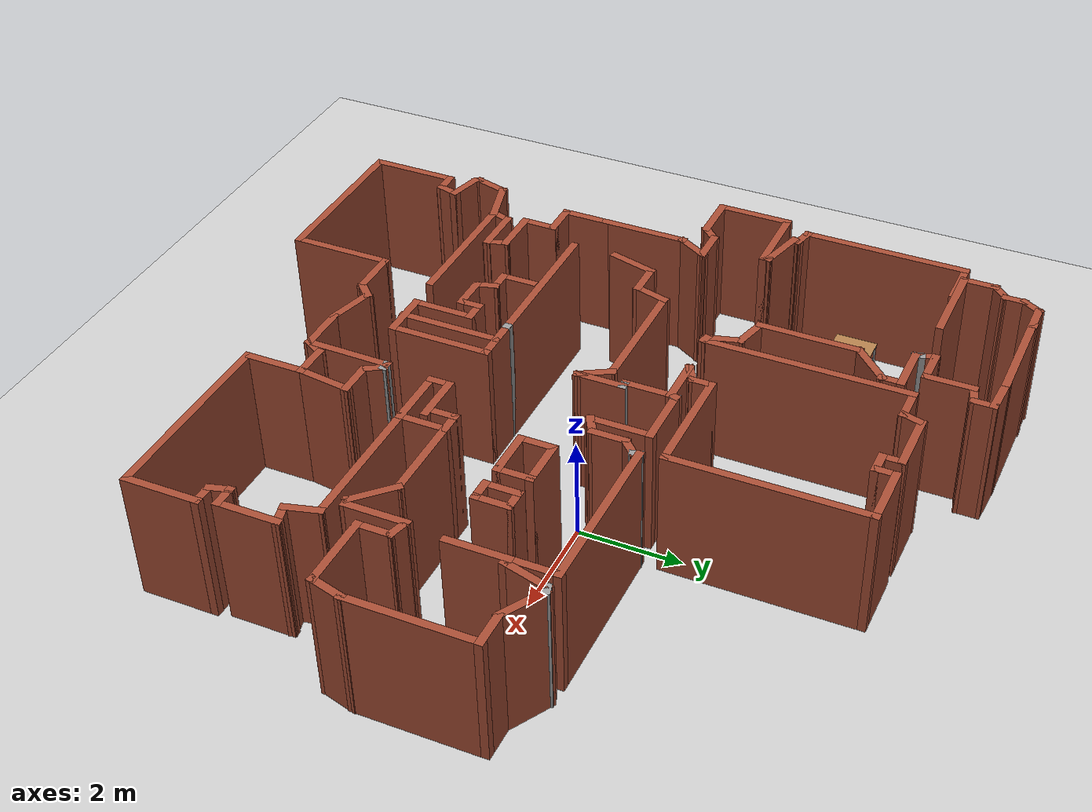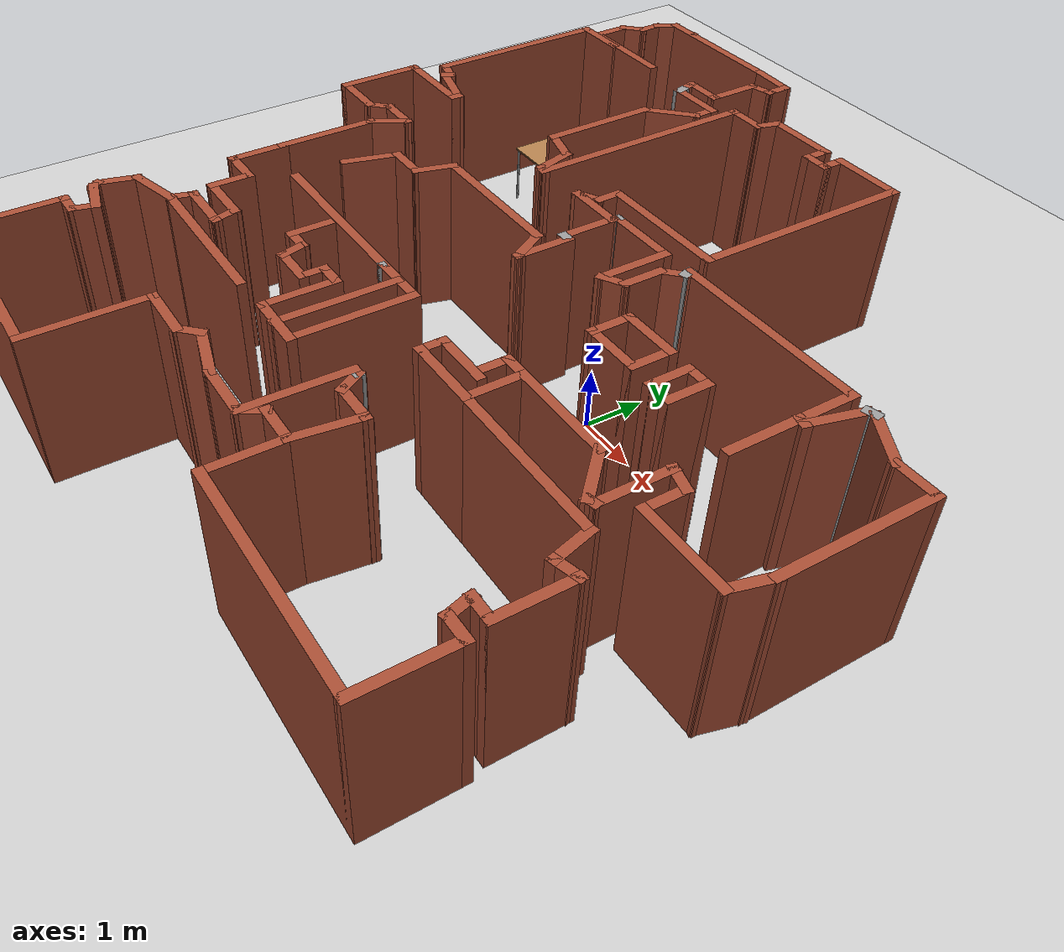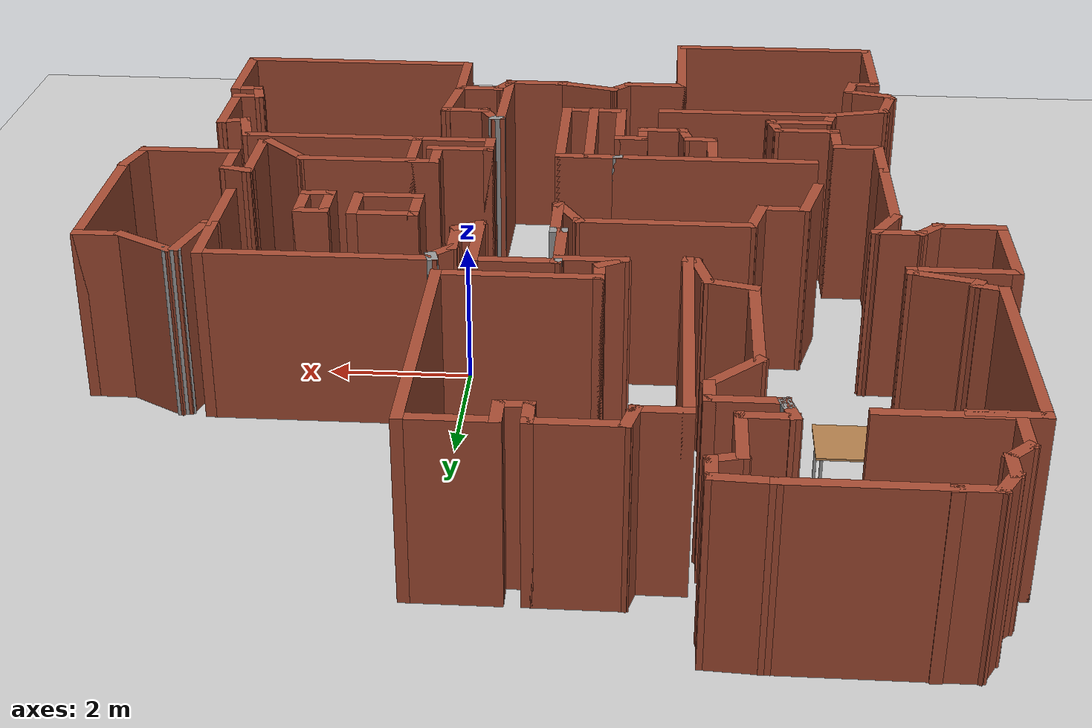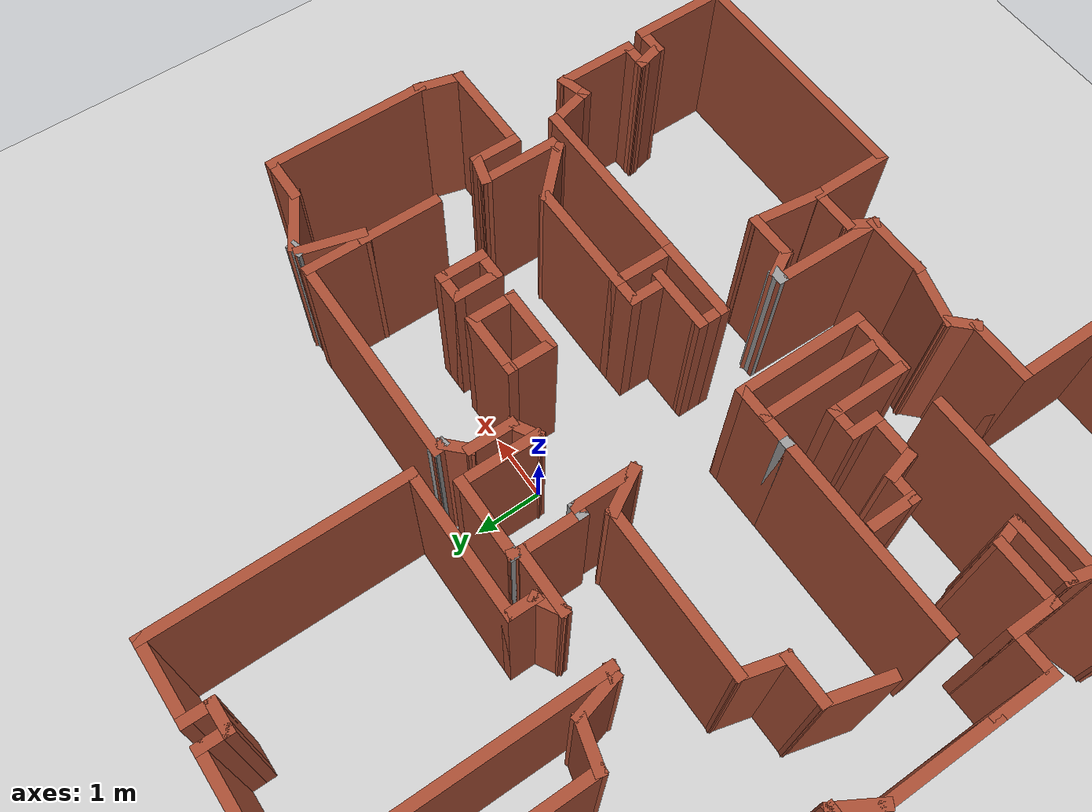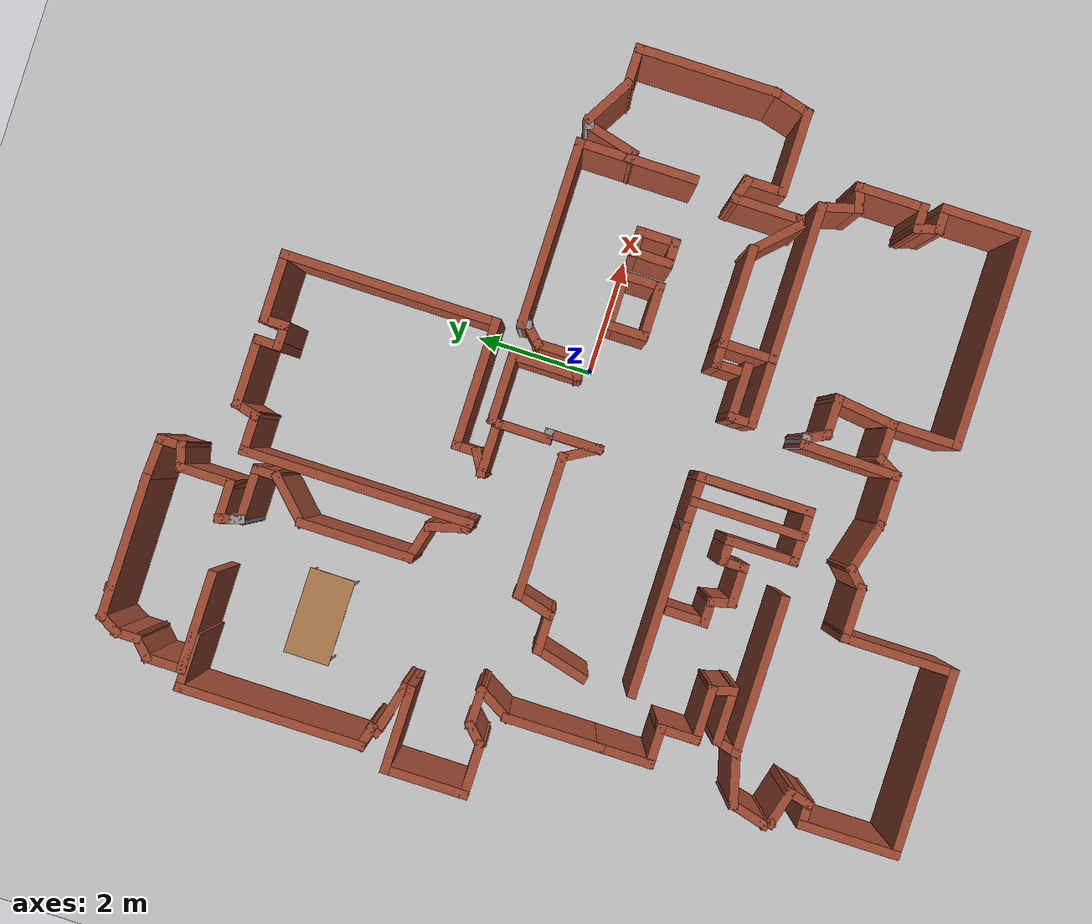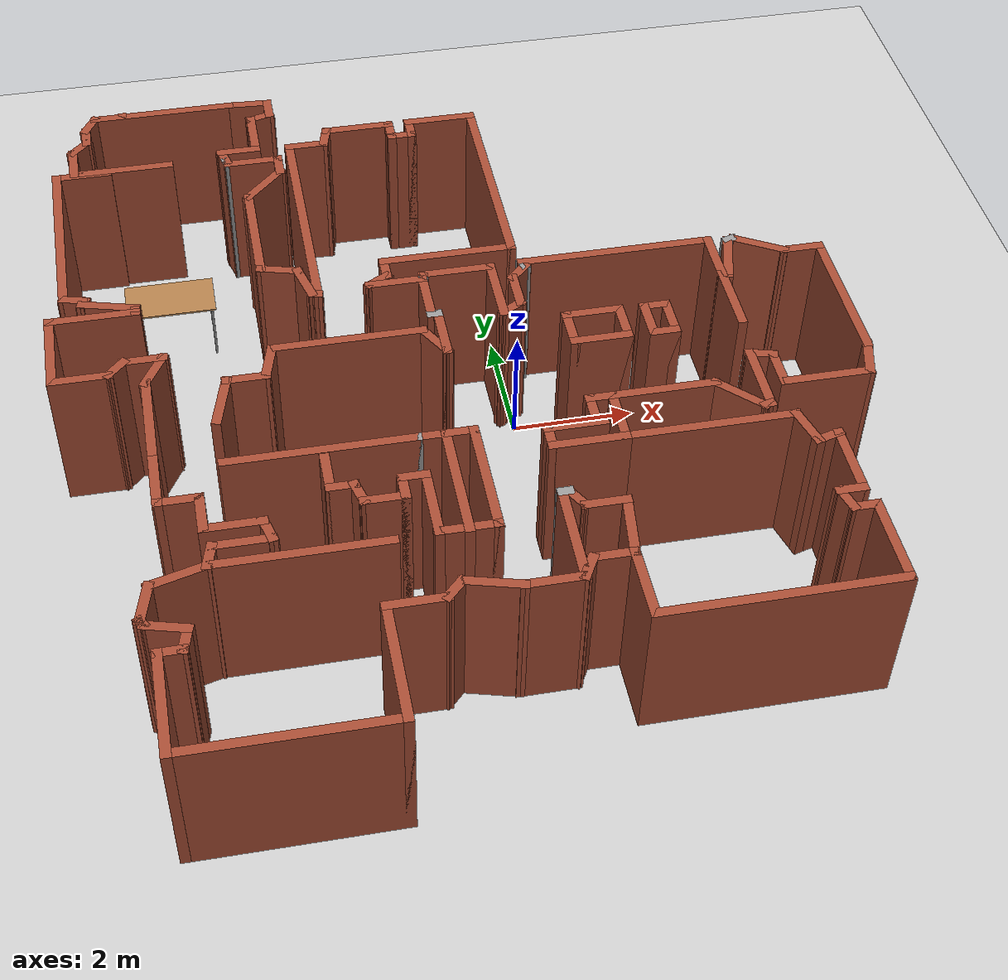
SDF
<sdf version="1.6">
 <world name="default">
  <light name="sun" type="directional">
   <pose>0 0 10 0 -0 0</pose>
   <diffuse>0.8 0.8 0.8 1</diffuse>
   <specular>0.2 0.2 0.2 1</specular>
   <attenuation>
    <range>1000</range>
    <constant>0.9</constant>
    <linear>0.01</linear>
    <quadratic>0.001</quadratic>
   </attenuation>
   <direction>-0.5 0.1 -0.9</direction>
  </light>
  <model name="ground_plane">
   <static>1</static>
   <link name="link">
    <collision name="collision">
     <geometry><plane><normal>0 0 1</normal><size>100 100</size></plane></geometry>
     <surface>
      <contact><collide_bitmask>65535</collide_bitmask></contact>
      <friction><ode><mu>100</mu><mu2>50</mu2></ode></friction>
     </surface>
    </collision>
    <visual name="visual">
     <cast_shadows>0</cast_shadows>
     <geometry><plane><normal>0 0 1</normal><size>100 100</size></plane></geometry>
     <material>
      <script><uri>file://media/materials/scripts/gazebo.material</uri><name>Gazebo/Grey</name></script>
     </material>
    </visual>
   </link>
  </model>
  <gravity>0 0 -9.8</gravity>
  <magnetic_field>6e-06 2.3e-05 -4.2e-05</magnetic_field>
  <atmosphere type="adiabatic"/>
  <physics name="default_physics" default="0" type="ode">
   <max_step_size>0.001</max_step_size>
   <real_time_factor>1</real_time_factor>
   <real_time_update_rate>1000</real_time_update_rate>
  </physics>
  <scene><ambient>0.4 0.4 0.4 1</ambient><background>0.7 0.7 0.7 1</background><shadows>1</shadows></scene>
  <audio><device>default</device></audio>
  <spherical_coordinates>
   <surface_model>EARTH_WGS84</surface_model>
   <latitude_deg>0</latitude_deg>
   <longitude_deg>0</longitude_deg>
   <elevation>0</elevation>
   <heading_deg>0</heading_deg>
  </spherical_coordinates>
  <model name="map_14">
   <pose>-1.02181 -0.3828 0 0 -0 0</pose>
   <link name="Wall_1">
    <collision name="Wall_1_Collision">
     <geometry><box><size>0.15 0.15 2.5</size></box></geometry>
     <pose>0 0 1.25 0 -0 0</pose>
    </collision>
    <visual name="Wall_1_Visual">
     <pose>0 0 1.25 0 -0 0</pose>
     <geometry><box><size>0.15 0.15 2.5</size></box></geometry>
     <material>
      <script><uri>file://media/materials/scripts/gazebo.material</uri><name>Gazebo/Bricks</name></script>
      <ambient>1 1 1 1</ambient>
     </material>
     <meta><layer>0</layer></meta>
    </visual>
    <pose>-4.77548 6.74677 0 0 -0 0</pose>
   </link>
   <link name="Wall_10">
    <collision name="Wall_10_Collision">
     <geometry><box><size>1.75 0.15 2.5</size></box></geometry>
     <pose>0 0 1.25 0 -0 0</pose>
    </collision>
    <visual name="Wall_10_Visual">
     <pose>0 0 1.25 0 -0 0</pose>
     <geometry><box><size>1.75 0.15 2.5</size></box></geometry>
     <material>
      <script><uri>file://media/materials/scripts/gazebo.material</uri><name>Gazebo/Bricks</name></script>
      <ambient>1 1 1 1</ambient>
     </material>
     <meta><layer>0</layer></meta>
    </visual>
    <pose>-4.87484 5.22304 0 0 -0 0</pose>
   </link>
   <link name="Wall_101">
    <collision name="Wall_101_Collision">
     <geometry><box><size>1.25 0.15 2.5</size></box></geometry>
     <pose>0 0 1.25 0 -0 0</pose>
    </collision>
    <visual name="Wall_101_Visual">
     <pose>0 0 1.25 0 -0 0</pose>
     <geometry><box><size>1.25 0.15 2.5</size></box></geometry>
     <material>
      <script><uri>file://media/materials/scripts/gazebo.material</uri><name>Gazebo/Bricks</name></script>
      <ambient>1 1 1 1</ambient>
     </material>
     <meta><layer>0</layer></meta>
    </visual>
    <pose>0.272904 1.65524 0 0 -0 3.14159</pose>
   </link>
   <link name="Wall_102">
    <collision name="Wall_102_Collision">
     <geometry><box><size>0.25 0.15 2.5</size></box></geometry>
     <pose>0 0 1.25 0 -0 0</pose>
    </collision>
    <visual name="Wall_102_Visual">
     <pose>0 0 1.25 0 -0 0</pose>
     <geometry><box><size>0.25 0.15 2.5</size></box></geometry>
     <material>
      <script><uri>file://media/materials/scripts/gazebo.material</uri><name>Gazebo/Bricks</name></script>
      <ambient>1 1 1 1</ambient>
     </material>
     <meta><layer>0</layer></meta>
    </visual>
    <pose>-0.290037 1.60695 0 0 -0 -1.8326</pose>
   </link>
   <link name="Wall_103">
    <collision name="Wall_103_Collision">
     <geometry><box><size>1 0.15 2.5</size></box></geometry>
     <pose>0 0 1.25 0 -0 0</pose>
    </collision>
    <visual name="Wall_103_Visual">
     <pose>0 0 1.25 0 -0 0</pose>
     <geometry><box><size>1 0.15 2.5</size></box></geometry>
     <material>
      <script><uri>file://media/materials/scripts/gazebo.material</uri><name>Gazebo/Bricks</name></script>
      <ambient>1 1 1 1</ambient>
     </material>
     <meta><layer>0</layer></meta>
    </visual>
    <pose>-0.727978 1.55865 0 0 -0 3.14159</pose>
   </link>
   <link name="Wall_104">
    <collision name="Wall_104_Collision">
     <geometry><box><size>0.5 0.15 2.5</size></box></geometry>
     <pose>0 0 1.25 0 -0 0</pose>
    </collision>
    <visual name="Wall_104_Visual">
     <pose>0 0 1.25 0 -0 0</pose>
     <geometry><box><size>0.5 0.15 2.5</size></box></geometry>
     <material>
      <script><uri>file://media/materials/scripts/gazebo.material</uri><name>Gazebo/Bricks</name></script>
      <ambient>1 1 1 1</ambient>
     </material>
     <meta><layer>0</layer></meta>
    </visual>
    <pose>-1.00142 1.64615 0 0 -0 0.523599</pose>
   </link>
   <link name="Wall_105">
    <collision name="Wall_105_Collision">
     <geometry><box><size>0.5 0.15 2.5</size></box></geometry>
     <pose>0 0 1.25 0 -0 0</pose>
    </collision>
    <visual name="Wall_105_Visual">
     <pose>0 0 1.25 0 -0 0</pose>
     <geometry><box><size>0.5 0.15 2.5</size></box></geometry>
     <material>
      <script><uri>file://media/materials/scripts/gazebo.material</uri><name>Gazebo/Bricks</name></script>
      <ambient>1 1 1 1</ambient>
     </material>
     <meta><layer>0</layer></meta>
    </visual>
    <pose>-0.849869 1.90865 0 0 -0 1.5708</pose>
   </link>
   <link name="Wall_106">
    <collision name="Wall_106_Collision">
     <geometry><box><size>2.25 0.15 2.5</size></box></geometry>
     <pose>0 0 1.25 0 -0 0</pose>
    </collision>
    <visual name="Wall_106_Visual">
     <pose>0 0 1.25 0 -0 0</pose>
     <geometry><box><size>2.25 0.15 2.5</size></box></geometry>
     <material>
      <script><uri>file://media/materials/scripts/gazebo.material</uri><name>Gazebo/Bricks</name></script>
      <ambient>1 1 1 1</ambient>
     </material>
     <meta><layer>0</layer></meta>
    </visual>
    <pose>0.200131 2.08365 0 0 -0 0</pose>
   </link>
   <link name="Wall_107">
    <collision name="Wall_107_Collision">
     <geometry><box><size>3.75 0.15 2.5</size></box></geometry>
     <pose>0 0 1.25 0 -0 0</pose>
    </collision>
    <visual name="Wall_107_Visual">
     <pose>0 0 1.25 0 -0 0</pose>
     <geometry><box><size>3.75 0.15 2.5</size></box></geometry>
     <material>
      <script><uri>file://media/materials/scripts/gazebo.material</uri><name>Gazebo/Bricks</name></script>
      <ambient>1 1 1 1</ambient>
     </material>
     <meta><layer>0</layer></meta>
    </visual>
    <pose>1.25013 3.88365 0 0 -0 1.5708</pose>
   </link>
   <link name="Wall_108">
    <collision name="Wall_108_Collision">
     <geometry><box><size>1.25 0.15 2.5</size></box></geometry>
     <pose>0 0 1.25 0 -0 0</pose>
    </collision>
    <visual name="Wall_108_Visual">
     <pose>0 0 1.25 0 -0 0</pose>
     <geometry><box><size>1.25 0.15 2.5</size></box></geometry>
     <material>
      <script><uri>file://media/materials/scripts/gazebo.material</uri><name>Gazebo/Bricks</name></script>
      <ambient>1 1 1 1</ambient>
     </material>
     <meta><layer>0</layer></meta>
    </visual>
    <pose>0.700131 5.68365 0 0 -0 3.14159</pose>
   </link>
   <link name="Wall_109">
    <collision name="Wall_109_Collision">
     <geometry><box><size>0.5 0.15 2.5</size></box></geometry>
     <pose>0 0 1.25 0 -0 0</pose>
    </collision>
    <visual name="Wall_109_Visual">
     <pose>0 0 1.25 0 -0 0</pose>
     <geometry><box><size>0.5 0.15 2.5</size></box></geometry>
     <material>
      <script><uri>file://media/materials/scripts/gazebo.material</uri><name>Gazebo/Bricks</name></script>
      <ambient>1 1 1 1</ambient>
     </material>
     <meta><layer>0</layer></meta>
    </visual>
    <pose>0.150131 5.50865 0 0 -0 -1.5708</pose>
   </link>
   <link name="Wall_110">
    <collision name="Wall_110_Collision">
     <geometry><box><size>0.5 0.15 2.5</size></box></geometry>
     <pose>0 0 1.25 0 -0 0</pose>
    </collision>
    <visual name="Wall_110_Visual">
     <pose>0 0 1.25 0 -0 0</pose>
     <geometry><box><size>0.5 0.15 2.5</size></box></geometry>
     <material>
      <script><uri>file://media/materials/scripts/gazebo.material</uri><name>Gazebo/Bricks</name></script>
      <ambient>1 1 1 1</ambient>
     </material>
     <meta><layer>0</layer></meta>
    </visual>
    <pose>-0.024869 5.33365 0 0 -0 3.14159</pose>
   </link>
   <link name="Wall_111">
    <collision name="Wall_111_Collision">
     <geometry><box><size>0.5 0.15 2.5</size></box></geometry>
     <pose>0 0 1.25 0 -0 0</pose>
    </collision>
    <visual name="Wall_111_Visual">
     <pose>0 0 1.25 0 -0 0</pose>
     <geometry><box><size>0.5 0.15 2.5</size></box></geometry>
     <material>
      <script><uri>file://media/materials/scripts/gazebo.material</uri><name>Gazebo/Bricks</name></script>
      <ambient>1 1 1 1</ambient>
     </material>
     <meta><layer>0</layer></meta>
    </visual>
    <pose>-0.199869 5.50865 0 0 -0 1.5708</pose>
   </link>
   <link name="Wall_112">
    <collision name="Wall_112_Collision">
     <geometry><box><size>1.25 0.15 2.5</size></box></geometry>
     <pose>0 0 1.25 0 -0 0</pose>
    </collision>
    <visual name="Wall_112_Visual">
     <pose>0 0 1.25 0 -0 0</pose>
     <geometry><box><size>1.25 0.15 2.5</size></box></geometry>
     <material>
      <script><uri>file://media/materials/scripts/gazebo.material</uri><name>Gazebo/Bricks</name></script>
      <ambient>1 1 1 1</ambient>
     </material>
     <meta><layer>0</layer></meta>
    </visual>
    <pose>-0.749869 5.68365 0 0 -0 3.14159</pose>
   </link>
   <link name="Wall_113">
    <collision name="Wall_113_Collision">
     <geometry><box><size>0.5 0.15 2.5</size></box></geometry>
     <pose>0 0 1.25 0 -0 0</pose>
    </collision>
    <visual name="Wall_113_Visual">
     <pose>0 0 1.25 0 -0 0</pose>
     <geometry><box><size>0.5 0.15 2.5</size></box></geometry>
     <material>
      <script><uri>file://media/materials/scripts/gazebo.material</uri><name>Gazebo/Bricks</name></script>
      <ambient>1 1 1 1</ambient>
     </material>
     <meta><layer>0</layer></meta>
    </visual>
    <pose>-1.34516 5.51461 0 0 -0 -1.8326</pose>
   </link>
   <link name="Wall_114">
    <collision name="Wall_114_Collision">
     <geometry><box><size>0.75 0.15 2.5</size></box></geometry>
     <pose>0 0 1.25 0 -0 0</pose>
    </collision>
    <visual name="Wall_114_Visual">
     <pose>0 0 1.25 0 -0 0</pose>
     <geometry><box><size>0.75 0.15 2.5</size></box></geometry>
     <material>
      <script><uri>file://media/materials/scripts/gazebo.material</uri><name>Gazebo/Bricks</name></script>
      <ambient>1 1 1 1</ambient>
     </material>
     <meta><layer>0</layer></meta>
    </visual>
    <pose>-1.69046 5.34558 0 0 -0 3.14159</pose>
   </link>
   <link name="Wall_115">
    <collision name="Wall_115_Collision">
     <geometry><box><size>4 0.15 2.5</size></box></geometry>
     <pose>0 0 1.25 0 -0 0</pose>
    </collision>
    <visual name="Wall_115_Visual">
     <pose>0 0 1.25 0 -0 0</pose>
     <geometry><box><size>4 0.15 2.5</size></box></geometry>
     <material>
      <script><uri>file://media/materials/scripts/gazebo.material</uri><name>Gazebo/Bricks</name></script>
      <ambient>1 1 1 1</ambient>
     </material>
     <meta><layer>0</layer></meta>
    </visual>
    <pose>-1.99046 3.42058 0 0 -0 -1.5708</pose>
   </link>
   <link name="Wall_116">
    <collision name="Wall_116_Collision">
     <geometry><box><size>0.25 0.15 2.5</size></box></geometry>
     <pose>0 0 1.25 0 -0 0</pose>
    </collision>
    <visual name="Wall_116_Visual">
     <pose>0 0 1.25 0 -0 0</pose>
     <geometry><box><size>0.25 0.15 2.5</size></box></geometry>
     <material>
      <script><uri>file://media/materials/scripts/gazebo.material</uri><name>Gazebo/Bricks</name></script>
      <ambient>1 1 1 1</ambient>
     </material>
     <meta><layer>0</layer></meta>
    </visual>
    <pose>-2.03875 1.50852 0 0 -0 2.87979</pose>
   </link>
   <link name="Wall_117">
    <collision name="Wall_117_Collision">
     <geometry><box><size>0.75 0.15 2.5</size></box></geometry>
     <pose>0 0 1.25 0 -0 0</pose>
    </collision>
    <visual name="Wall_117_Visual">
     <pose>0 0 1.25 0 -0 0</pose>
     <geometry><box><size>0.75 0.15 2.5</size></box></geometry>
     <material>
      <script><uri>file://media/materials/scripts/gazebo.material</uri><name>Gazebo/Bricks</name></script>
      <ambient>1 1 1 1</ambient>
     </material>
     <meta><layer>0</layer></meta>
    </visual>
    <pose>-2.16469 1.81124 0 0 -0 1.8326</pose>
   </link>
   <link name="Wall_118">
    <collision name="Wall_118_Collision">
     <geometry><box><size>0.75 0.15 2.5</size></box></geometry>
     <pose>0 0 1.25 0 -0 0</pose>
    </collision>
    <visual name="Wall_118_Visual">
     <pose>0 0 1.25 0 -0 0</pose>
     <geometry><box><size>0.75 0.15 2.5</size></box></geometry>
     <material>
      <script><uri>file://media/materials/scripts/gazebo.material</uri><name>Gazebo/Bricks</name></script>
      <ambient>1 1 1 1</ambient>
     </material>
     <meta><layer>0</layer></meta>
    </visual>
    <pose>-2.53212 2.17866 0 0 -0 2.87979</pose>
   </link>
   <link name="Wall_119">
    <collision name="Wall_119_Collision">
     <geometry><box><size>2 0.15 2.5</size></box></geometry>
     <pose>0 0 1.25 0 -0 0</pose>
    </collision>
    <visual name="Wall_119_Visual">
     <pose>0 0 1.25 0 -0 0</pose>
     <geometry><box><size>2 0.15 2.5</size></box></geometry>
     <material>
      <script><uri>file://media/materials/scripts/gazebo.material</uri><name>Gazebo/Bricks</name></script>
      <ambient>1 1 1 1</ambient>
     </material>
     <meta><layer>0</layer></meta>
    </visual>
    <pose>-2.8219 3.18131 0 0 -0 1.5708</pose>
   </link>
   <link name="Wall_12">
    <collision name="Wall_12_Collision">
     <geometry><box><size>1 0.15 2.5</size></box></geometry>
     <pose>0 0 1.25 0 -0 0</pose>
    </collision>
    <visual name="Wall_12_Visual">
     <pose>0 0 1.25 0 -0 0</pose>
     <geometry><box><size>1 0.15 2.5</size></box></geometry>
     <material>
      <script><uri>file://media/materials/scripts/gazebo.material</uri><name>Gazebo/Bricks</name></script>
      <ambient>1 1 1 1</ambient>
     </material>
     <meta><layer>0</layer></meta>
    </visual>
    <pose>-5.54789 5.17389 0 0 -0 3.14159</pose>
   </link>
   <link name="Wall_120">
    <collision name="Wall_120_Collision">
     <geometry><box><size>1 0.15 2.5</size></box></geometry>
     <pose>0 0 1.25 0 -0 0</pose>
    </collision>
    <visual name="Wall_120_Visual">
     <pose>0 0 1.25 0 -0 0</pose>
     <geometry><box><size>1 0.15 2.5</size></box></geometry>
     <material>
      <script><uri>file://media/materials/scripts/gazebo.material</uri><name>Gazebo/Bricks</name></script>
      <ambient>1 1 1 1</ambient>
     </material>
     <meta><layer>0</layer></meta>
    </visual>
    <pose>-2.52137 4.40683 0 0 -0 0.785398</pose>
   </link>
   <link name="Wall_121">
    <collision name="Wall_121_Collision">
     <geometry><box><size>0.5 0.15 2.5</size></box></geometry>
     <pose>0 0 1.25 0 -0 0</pose>
    </collision>
    <visual name="Wall_121_Visual">
     <pose>0 0 1.25 0 -0 0</pose>
     <geometry><box><size>0.5 0.15 2.5</size></box></geometry>
     <material>
      <script><uri>file://media/materials/scripts/gazebo.material</uri><name>Gazebo/Bricks</name></script>
      <ambient>1 1 1 1</ambient>
     </material>
     <meta><layer>0</layer></meta>
    </visual>
    <pose>-2.22085 4.88235 0 0 -0 1.5708</pose>
   </link>
   <link name="Wall_123">
    <collision name="Wall_123_Collision">
     <geometry><box><size>0.25 0.15 2.5</size></box></geometry>
     <pose>0 0 1.25 0 -0 0</pose>
    </collision>
    <visual name="Wall_123_Visual">
     <pose>0 0 1.25 0 -0 0</pose>
     <geometry><box><size>0.25 0.15 2.5</size></box></geometry>
     <material>
      <script><uri>file://media/materials/scripts/gazebo.material</uri><name>Gazebo/Grey</name></script>
      <ambient>1 1 1 1</ambient>
     </material>
     <meta><layer>0</layer></meta>
    </visual>
    <pose>-3.08379 5.10564 0 0 -0 1.8326</pose>
   </link>
   <link name="Wall_126">
    <collision name="Wall_126_Collision">
     <geometry><box><size>0.25 0.15 2.5</size></box></geometry>
     <pose>0 0 1.25 0 -0 0</pose>
    </collision>
    <visual name="Wall_126_Visual">
     <pose>0 0 1.25 0 -0 0</pose>
     <geometry><box><size>0.25 0.15 2.5</size></box></geometry>
     <material>
      <script><uri>file://media/materials/scripts/gazebo.material</uri><name>Gazebo/Grey</name></script>
      <ambient>1 1 1 1</ambient>
     </material>
     <meta><layer>0</layer></meta>
    </visual>
    <pose>-3.08379 5.10564 0 0 -0 1.8326</pose>
   </link>
   <link name="Wall_129">
    <collision name="Wall_129_Collision">
     <geometry><box><size>1 0.15 2.5</size></box></geometry>
     <pose>0 0 1.25 0 -0 0</pose>
    </collision>
    <visual name="Wall_129_Visual">
     <pose>0 0 1.25 0 -0 0</pose>
     <geometry><box><size>1 0.15 2.5</size></box></geometry>
     <material>
      <script><uri>file://media/materials/scripts/gazebo.material</uri><name>Gazebo/Bricks</name></script>
      <ambient>1 1 1 1</ambient>
     </material>
     <meta><layer>0</layer></meta>
    </visual>
    <pose>-2.64585 5.05735 0 0 -0 3.14159</pose>
   </link>
   <link name="Wall_13">
    <collision name="Wall_13_Collision">
     <geometry><box><size>3.25 0.15 2.5</size></box></geometry>
     <pose>0 0 1.25 0 -0 0</pose>
    </collision>
    <visual name="Wall_13_Visual">
     <pose>0 0 1.25 0 -0 0</pose>
     <geometry><box><size>3.25 0.15 2.5</size></box></geometry>
     <material>
      <script><uri>file://media/materials/scripts/gazebo.material</uri><name>Gazebo/Bricks</name></script>
      <ambient>1 1 1 1</ambient>
     </material>
     <meta><layer>0</layer></meta>
    </visual>
    <pose>-5.97289 3.62389 0 0 -0 -1.5708</pose>
   </link>
   <link name="Wall_130">
    <collision name="Wall_130_Collision">
     <geometry><box><size>0.5 0.15 2.5</size></box></geometry>
     <pose>0 0 1.25 0 -0 0</pose>
    </collision>
    <visual name="Wall_130_Visual">
     <pose>0 0 1.25 0 -0 0</pose>
     <geometry><box><size>0.5 0.15 2.5</size></box></geometry>
     <material>
      <script><uri>file://media/materials/scripts/gazebo.material</uri><name>Gazebo/Bricks</name></script>
      <ambient>1 1 1 1</ambient>
     </material>
     <meta><layer>0</layer></meta>
    </visual>
    <pose>-3.11615 5.22638 0 0 -0 1.8326</pose>
   </link>
   <link name="Wall_133">
    <collision name="Wall_133_Collision">
     <geometry><box><size>0.75 0.15 2.5</size></box></geometry>
     <pose>0 0 1.25 0 -0 0</pose>
    </collision>
    <visual name="Wall_133_Visual">
     <pose>0 0 1.25 0 -0 0</pose>
     <geometry><box><size>0.75 0.15 2.5</size></box></geometry>
     <material>
      <script><uri>file://media/materials/scripts/gazebo.material</uri><name>Gazebo/Bricks</name></script>
      <ambient>1 1 1 1</ambient>
     </material>
     <meta><layer>0</layer></meta>
    </visual>
    <pose>-2.86144 5.39542 0 0 -0 0</pose>
   </link>
   <link name="Wall_134">
    <collision name="Wall_134_Collision">
     <geometry><box><size>1 0.15 2.5</size></box></geometry>
     <pose>0 0 1.25 0 -0 0</pose>
    </collision>
    <visual name="Wall_134_Visual">
     <pose>0 0 1.25 0 -0 0</pose>
     <geometry><box><size>1 0.15 2.5</size></box></geometry>
     <material>
      <script><uri>file://media/materials/scripts/gazebo.material</uri><name>Gazebo/Bricks</name></script>
      <ambient>1 1 1 1</ambient>
     </material>
     <meta><layer>0</layer></meta>
    </visual>
    <pose>-2.56144 5.82042 0 0 -0 1.5708</pose>
   </link>
   <link name="Wall_135">
    <collision name="Wall_135_Collision">
     <geometry><box><size>0.5 0.15 2.5</size></box></geometry>
     <pose>0 0 1.25 0 -0 0</pose>
    </collision>
    <visual name="Wall_135_Visual">
     <pose>0 0 1.25 0 -0 0</pose>
     <geometry><box><size>0.5 0.15 2.5</size></box></geometry>
     <material>
      <script><uri>file://media/materials/scripts/gazebo.material</uri><name>Gazebo/Bricks</name></script>
      <ambient>1 1 1 1</ambient>
     </material>
     <meta><layer>0</layer></meta>
    </visual>
    <pose>-2.3924 6.29071 0 0 -0 0.261799</pose>
   </link>
   <link name="Wall_136">
    <collision name="Wall_136_Collision">
     <geometry><box><size>0.5 0.15 2.5</size></box></geometry>
     <pose>0 0 1.25 0 -0 0</pose>
    </collision>
    <visual name="Wall_136_Visual">
     <pose>0 0 1.25 0 -0 0</pose>
     <geometry><box><size>0.5 0.15 2.5</size></box></geometry>
     <material>
      <script><uri>file://media/materials/scripts/gazebo.material</uri><name>Gazebo/Bricks</name></script>
      <ambient>1 1 1 1</ambient>
     </material>
     <meta><layer>0</layer></meta>
    </visual>
    <pose>-2.22337 6.51101 0 0 -0 1.5708</pose>
   </link>
   <link name="Wall_137">
    <collision name="Wall_137_Collision">
     <geometry><box><size>0.830025 0.15 2.5</size></box></geometry>
     <pose>0 0 1.25 0 -0 0</pose>
    </collision>
    <visual name="Wall_137_Visual">
     <pose>0 0 1.25 0 -0 0</pose>
     <geometry><box><size>0.830025 0.15 2.5</size></box></geometry>
     <material>
      <script><uri>file://media/materials/scripts/gazebo.material</uri><name>Gazebo/Bricks</name></script>
      <ambient>1 1 1 1</ambient>
     </material>
     <meta><layer>0</layer></meta>
    </visual>
    <pose>-2.56286 6.70482 0 0 -0 3.08623</pose>
   </link>
   <link name="Wall_14">
    <collision name="Wall_14_Collision">
     <geometry><box><size>0.5 0.15 2.5</size></box></geometry>
     <pose>0 0 1.25 0 -0 0</pose>
    </collision>
    <visual name="Wall_14_Visual">
     <pose>0 0 1.25 0 -0 0</pose>
     <geometry><box><size>0.5 0.15 2.5</size></box></geometry>
     <material>
      <script><uri>file://media/materials/scripts/gazebo.material</uri><name>Gazebo/Bricks</name></script>
      <ambient>1 1 1 1</ambient>
     </material>
     <meta><layer>0</layer></meta>
    </visual>
    <pose>-5.80385 2.0286 0 0 -0 -0.261799</pose>
   </link>
   <link name="Wall_140">
    <collision name="Wall_140_Collision">
     <geometry><box><size>1.25 0.15 2.5</size></box></geometry>
     <pose>0 0 1.25 0 -0 0</pose>
    </collision>
    <visual name="Wall_140_Visual">
     <pose>0 0 1.25 0 -0 0</pose>
     <geometry><box><size>1.25 0.15 2.5</size></box></geometry>
     <material>
      <script><uri>file://media/materials/scripts/gazebo.material</uri><name>Gazebo/Bricks</name></script>
      <ambient>1 1 1 1</ambient>
     </material>
     <meta><layer>0</layer></meta>
    </visual>
    <pose>4.44762 0.274324 0 0 -0 -1.5708</pose>
   </link>
   <link name="Wall_142">
    <collision name="Wall_142_Collision">
     <geometry><box><size>0.75 0.15 2.5</size></box></geometry>
     <pose>0 0 1.25 0 -0 0</pose>
    </collision>
    <visual name="Wall_142_Visual">
     <pose>0 0 1.25 0 -0 0</pose>
     <geometry><box><size>0.75 0.15 2.5</size></box></geometry>
     <material>
      <script><uri>file://media/materials/scripts/gazebo.material</uri><name>Gazebo/Bricks</name></script>
      <ambient>1 1 1 1</ambient>
     </material>
     <meta><layer>0</layer></meta>
    </visual>
    <pose>1.77003 0.016461 0 0 -0 -1.5708</pose>
   </link>
   <link name="Wall_143">
    <collision name="Wall_143_Collision">
     <geometry><box><size>1 0.15 2.5</size></box></geometry>
     <pose>0 0 1.25 0 -0 0</pose>
    </collision>
    <visual name="Wall_143_Visual">
     <pose>0 0 1.25 0 -0 0</pose>
     <geometry><box><size>1 0.15 2.5</size></box></geometry>
     <material>
      <script><uri>file://media/materials/scripts/gazebo.material</uri><name>Gazebo/Bricks</name></script>
      <ambient>1 1 1 1</ambient>
     </material>
     <meta><layer>0</layer></meta>
    </visual>
    <pose>2.19503 -0.283539 0 0 -0 0</pose>
   </link>
   <link name="Wall_144">
    <collision name="Wall_144_Collision">
     <geometry><box><size>0.75 0.15 2.5</size></box></geometry>
     <pose>0 0 1.25 0 -0 0</pose>
    </collision>
    <visual name="Wall_144_Visual">
     <pose>0 0 1.25 0 -0 0</pose>
     <geometry><box><size>0.75 0.15 2.5</size></box></geometry>
     <material>
      <script><uri>file://media/materials/scripts/gazebo.material</uri><name>Gazebo/Bricks</name></script>
      <ambient>1 1 1 1</ambient>
     </material>
     <meta><layer>0</layer></meta>
    </visual>
    <pose>2.62003 0.016461 0 0 -0 1.5708</pose>
   </link>
   <link name="Wall_145">
    <collision name="Wall_145_Collision">
     <geometry><box><size>1 0.15 2.5</size></box></geometry>
     <pose>0 0 1.25 0 -0 0</pose>
    </collision>
    <visual name="Wall_145_Visual">
     <pose>0 0 1.25 0 -0 0</pose>
     <geometry><box><size>1 0.15 2.5</size></box></geometry>
     <material>
      <script><uri>file://media/materials/scripts/gazebo.material</uri><name>Gazebo/Bricks</name></script>
      <ambient>1 1 1 1</ambient>
     </material>
     <meta><layer>0</layer></meta>
    </visual>
    <pose>2.19503 0.316462 0 0 -0 3.14159</pose>
   </link>
   <link name="Wall_148">
    <collision name="Wall_148_Collision">
     <geometry><box><size>0.75 0.15 2.5</size></box></geometry>
     <pose>0 0 1.25 0 -0 0</pose>
    </collision>
    <visual name="Wall_148_Visual">
     <pose>0 0 1.25 0 -0 0</pose>
     <geometry><box><size>0.75 0.15 2.5</size></box></geometry>
     <material>
      <script><uri>file://media/materials/scripts/gazebo.material</uri><name>Gazebo/Bricks</name></script>
      <ambient>1 1 1 1</ambient>
     </material>
     <meta><layer>0</layer></meta>
    </visual>
    <pose>3.02129 -0.004847 0 0 -0 -1.5708</pose>
   </link>
   <link name="Wall_149">
    <collision name="Wall_149_Collision">
     <geometry><box><size>0.5 0.15 2.5</size></box></geometry>
     <pose>0 0 1.25 0 -0 0</pose>
    </collision>
    <visual name="Wall_149_Visual">
     <pose>0 0 1.25 0 -0 0</pose>
     <geometry><box><size>0.5 0.15 2.5</size></box></geometry>
     <material>
      <script><uri>file://media/materials/scripts/gazebo.material</uri><name>Gazebo/Bricks</name></script>
      <ambient>1 1 1 1</ambient>
     </material>
     <meta><layer>0</layer></meta>
    </visual>
    <pose>3.19629 -0.304847 0 0 -0 0</pose>
   </link>
   <link name="Wall_15">
    <collision name="Wall_15_Collision">
     <geometry><box><size>0.25 0.15 2.5</size></box></geometry>
     <pose>0 0 1.25 0 -0 0</pose>
    </collision>
    <visual name="Wall_15_Visual">
     <pose>0 0 1.25 0 -0 0</pose>
     <geometry><box><size>0.25 0.15 2.5</size></box></geometry>
     <material>
      <script><uri>file://media/materials/scripts/gazebo.material</uri><name>Gazebo/Bricks</name></script>
      <ambient>1 1 1 1</ambient>
     </material>
     <meta><layer>0</layer></meta>
    </visual>
    <pose>-5.65981 1.94 0 0 -0 -2.0944</pose>
   </link>
   <link name="Wall_150">
    <collision name="Wall_150_Collision">
     <geometry><box><size>0.75 0.15 2.5</size></box></geometry>
     <pose>0 0 1.25 0 -0 0</pose>
    </collision>
    <visual name="Wall_150_Visual">
     <pose>0 0 1.25 0 -0 0</pose>
     <geometry><box><size>0.75 0.15 2.5</size></box></geometry>
     <material>
      <script><uri>file://media/materials/scripts/gazebo.material</uri><name>Gazebo/Bricks</name></script>
      <ambient>1 1 1 1</ambient>
     </material>
     <meta><layer>0</layer></meta>
    </visual>
    <pose>3.37129 -0.004847 0 0 -0 1.5708</pose>
   </link>
   <link name="Wall_151">
    <collision name="Wall_151_Collision">
     <geometry><box><size>0.5 0.15 2.5</size></box></geometry>
     <pose>0 0 1.25 0 -0 0</pose>
    </collision>
    <visual name="Wall_151_Visual">
     <pose>0 0 1.25 0 -0 0</pose>
     <geometry><box><size>0.5 0.15 2.5</size></box></geometry>
     <material>
      <script><uri>file://media/materials/scripts/gazebo.material</uri><name>Gazebo/Bricks</name></script>
      <ambient>1 1 1 1</ambient>
     </material>
     <meta><layer>0</layer></meta>
    </visual>
    <pose>3.19629 0.295153 0 0 -0 3.14159</pose>
   </link>
   <link name="Wall_153">
    <collision name="Wall_153_Collision">
     <geometry><box><size>1 0.15 2.5</size></box></geometry>
     <pose>0 0 1.25 0 -0 0</pose>
    </collision>
    <visual name="Wall_153_Visual">
     <pose>0 0 1.25 0 -0 0</pose>
     <geometry><box><size>1 0.15 2.5</size></box></geometry>
     <material>
      <script><uri>file://media/materials/scripts/gazebo.material</uri><name>Gazebo/Bricks</name></script>
      <ambient>1 1 1 1</ambient>
     </material>
     <meta><layer>0</layer></meta>
    </visual>
    <pose>-0.302978 1.13365 0 0 -0 -1.5708</pose>
   </link>
   <link name="Wall_154">
    <collision name="Wall_154_Collision">
     <geometry><box><size>0.25 0.15 2.5</size></box></geometry>
     <pose>0 0 1.25 0 -0 0</pose>
    </collision>
    <visual name="Wall_154_Visual">
     <pose>0 0 1.25 0 -0 0</pose>
     <geometry><box><size>0.25 0.15 2.5</size></box></geometry>
     <material>
      <script><uri>file://media/materials/scripts/gazebo.material</uri><name>Gazebo/Grey</name></script>
      <ambient>1 1 1 1</ambient>
     </material>
     <meta><layer>0</layer></meta>
    </visual>
    <pose>-0.252978 0.708652 0 0 -0 0</pose>
   </link>
   <link name="Wall_155">
    <collision name="Wall_155_Collision">
     <geometry><box><size>1 0.15 2.5</size></box></geometry>
     <pose>0 0 1.25 0 -0 0</pose>
    </collision>
    <visual name="Wall_155_Visual">
     <pose>0 0 1.25 0 -0 0</pose>
     <geometry><box><size>1 0.15 2.5</size></box></geometry>
     <material>
      <script><uri>file://media/materials/scripts/gazebo.material</uri><name>Gazebo/Bricks</name></script>
      <ambient>1 1 1 1</ambient>
     </material>
     <meta><layer>0</layer></meta>
    </visual>
    <pose>-0.202978 0.283651 0 0 -0 -1.5708</pose>
   </link>
   <link name="Wall_156">
    <collision name="Wall_156_Collision">
     <geometry><box><size>0.15 0.15 2.5</size></box></geometry>
     <pose>0 0 1.25 0 -0 0</pose>
    </collision>
    <visual name="Wall_156_Visual">
     <pose>0 0 1.25 0 -0 0</pose>
     <geometry><box><size>0.15 0.15 2.5</size></box></geometry>
     <material>
      <script><uri>file://media/materials/scripts/gazebo.material</uri><name>Gazebo/Bricks</name></script>
      <ambient>1 1 1 1</ambient>
     </material>
     <meta><layer>0</layer></meta>
    </visual>
    <pose>-0.202978 -0.141349 0 0 -0 0</pose>
   </link>
   <link name="Wall_157">
    <collision name="Wall_157_Collision">
     <geometry><box><size>0.75 0.15 2.5</size></box></geometry>
     <pose>0 0 1.25 0 -0 0</pose>
    </collision>
    <visual name="Wall_157_Visual">
     <pose>0 0 1.25 0 -0 0</pose>
     <geometry><box><size>0.75 0.15 2.5</size></box></geometry>
     <material>
      <script><uri>file://media/materials/scripts/gazebo.material</uri><name>Gazebo/Bricks</name></script>
      <ambient>1 1 1 1</ambient>
     </material>
     <meta><layer>0</layer></meta>
    </visual>
    <pose>-0.352978 0.118459 0 0 -0 2.0944</pose>
   </link>
   <link name="Wall_158">
    <collision name="Wall_158_Collision">
     <geometry><box><size>2.5 0.15 2.5</size></box></geometry>
     <pose>0 0 1.25 0 -0 0</pose>
    </collision>
    <visual name="Wall_158_Visual">
     <pose>0 0 1.25 0 -0 0</pose>
     <geometry><box><size>2.5 0.15 2.5</size></box></geometry>
     <material>
      <script><uri>file://media/materials/scripts/gazebo.material</uri><name>Gazebo/Bricks</name></script>
      <ambient>1 1 1 1</ambient>
     </material>
     <meta><layer>0</layer></meta>
    </visual>
    <pose>-1.67798 0.378267 0 0 -0 3.14159</pose>
   </link>
   <link name="Wall_159">
    <collision name="Wall_159_Collision">
     <geometry><box><size>0.75 0.15 2.5</size></box></geometry>
     <pose>0 0 1.25 0 -0 0</pose>
    </collision>
    <visual name="Wall_159_Visual">
     <pose>0 0 1.25 0 -0 0</pose>
     <geometry><box><size>0.75 0.15 2.5</size></box></geometry>
     <material>
      <script><uri>file://media/materials/scripts/gazebo.material</uri><name>Gazebo/Bricks</name></script>
      <ambient>1 1 1 1</ambient>
     </material>
     <meta><layer>0</layer></meta>
    </visual>
    <pose>-2.93062 0.088489 0 0 -0 -1.8326</pose>
   </link>
   <link name="Wall_16">
    <collision name="Wall_16_Collision">
     <geometry><box><size>1 0.15 2.5</size></box></geometry>
     <pose>0 0 1.25 0 -0 0</pose>
    </collision>
    <visual name="Wall_16_Visual">
     <pose>0 0 1.25 0 -0 0</pose>
     <geometry><box><size>1 0.15 2.5</size></box></geometry>
     <material>
      <script><uri>file://media/materials/scripts/gazebo.material</uri><name>Gazebo/Bricks</name></script>
      <ambient>1 1 1 1</ambient>
     </material>
     <meta><layer>0</layer></meta>
    </visual>
    <pose>-5.2743 1.7867 0 0 -0 -0.261799</pose>
   </link>
   <link name="Wall_160">
    <collision name="Wall_160_Collision">
     <geometry><box><size>0.75 0.15 2.5</size></box></geometry>
     <pose>0 0 1.25 0 -0 0</pose>
    </collision>
    <visual name="Wall_160_Visual">
     <pose>0 0 1.25 0 -0 0</pose>
     <geometry><box><size>0.75 0.15 2.5</size></box></geometry>
     <material>
      <script><uri>file://media/materials/scripts/gazebo.material</uri><name>Gazebo/Bricks</name></script>
      <ambient>1 1 1 1</ambient>
     </material>
     <meta><layer>0</layer></meta>
    </visual>
    <pose>-3.30827 -0.201289 0 0 -0 3.14159</pose>
   </link>
   <link name="Wall_161">
    <collision name="Wall_161_Collision">
     <geometry><box><size>1 0.15 2.5</size></box></geometry>
     <pose>0 0 1.25 0 -0 0</pose>
    </collision>
    <visual name="Wall_161_Visual">
     <pose>0 0 1.25 0 -0 0</pose>
     <geometry><box><size>1 0.15 2.5</size></box></geometry>
     <material>
      <script><uri>file://media/materials/scripts/gazebo.material</uri><name>Gazebo/Bricks</name></script>
      <ambient>1 1 1 1</ambient>
     </material>
     <meta><layer>0</layer></meta>
    </visual>
    <pose>-3.71827 -0.611807 0 0 -0 -1.8326</pose>
   </link>
   <link name="Wall_163">
    <collision name="Wall_163_Collision">
     <geometry><box><size>3 0.15 2.5</size></box></geometry>
     <pose>0 0 1.25 0 -0 0</pose>
    </collision>
    <visual name="Wall_163_Visual">
     <pose>0 0 1.25 0 -0 0</pose>
     <geometry><box><size>3 0.15 2.5</size></box></geometry>
     <material>
      <script><uri>file://media/materials/scripts/gazebo.material</uri><name>Gazebo/Bricks</name></script>
      <ambient>1 1 1 1</ambient>
     </material>
     <meta><layer>0</layer></meta>
    </visual>
    <pose>-2.39233 -1.87711 0 0 -0 0</pose>
   </link>
   <link name="Wall_164">
    <collision name="Wall_164_Collision">
     <geometry><box><size>0.15 0.15 2.5</size></box></geometry>
     <pose>0 0 1.25 0 -0 0</pose>
    </collision>
    <visual name="Wall_164_Visual">
     <pose>0 0 1.25 0 -0 0</pose>
     <geometry><box><size>0.15 0.15 2.5</size></box></geometry>
     <material>
      <script><uri>file://media/materials/scripts/gazebo.material</uri><name>Gazebo/Grey</name></script>
      <ambient>1 1 1 1</ambient>
     </material>
     <meta><layer>0</layer></meta>
    </visual>
    <pose>-0.967326 -1.87711 0 0 -0 0</pose>
   </link>
   <link name="Wall_165">
    <collision name="Wall_165_Collision">
     <geometry><box><size>1 0.15 2.5</size></box></geometry>
     <pose>0 0 1.25 0 -0 0</pose>
    </collision>
    <visual name="Wall_165_Visual">
     <pose>0 0 1.25 0 -0 0</pose>
     <geometry><box><size>1 0.15 2.5</size></box></geometry>
     <material>
      <script><uri>file://media/materials/scripts/gazebo.material</uri><name>Gazebo/Bricks</name></script>
      <ambient>1 1 1 1</ambient>
     </material>
     <meta><layer>0</layer></meta>
    </visual>
    <pose>-0.542326 -1.87711 0 0 -0 0</pose>
   </link>
   <link name="Wall_166">
    <collision name="Wall_166_Collision">
     <geometry><box><size>2 0.15 2.5</size></box></geometry>
     <pose>0 0 1.25 0 -0 0</pose>
    </collision>
    <visual name="Wall_166_Visual">
     <pose>0 0 1.25 0 -0 0</pose>
     <geometry><box><size>2 0.15 2.5</size></box></geometry>
     <material>
      <script><uri>file://media/materials/scripts/gazebo.material</uri><name>Gazebo/Bricks</name></script>
      <ambient>1 1 1 1</ambient>
     </material>
     <meta><layer>0</layer></meta>
    </visual>
    <pose>-0.117326 -2.80211 0 0 -0 -1.5708</pose>
   </link>
   <link name="Wall_167">
    <collision name="Wall_167_Collision">
     <geometry><box><size>1 0.15 2.5</size></box></geometry>
     <pose>0 0 1.25 0 -0 0</pose>
    </collision>
    <visual name="Wall_167_Visual">
     <pose>0 0 1.25 0 -0 0</pose>
     <geometry><box><size>1 0.15 2.5</size></box></geometry>
     <material>
      <script><uri>file://media/materials/scripts/gazebo.material</uri><name>Gazebo/Bricks</name></script>
      <ambient>1 1 1 1</ambient>
     </material>
     <meta><layer>0</layer></meta>
    </visual>
    <pose>-0.542326 -3.72711 0 0 -0 3.14159</pose>
   </link>
   <link name="Wall_168">
    <collision name="Wall_168_Collision">
     <geometry><box><size>1.25 0.15 2.5</size></box></geometry>
     <pose>0 0 1.25 0 -0 0</pose>
    </collision>
    <visual name="Wall_168_Visual">
     <pose>0 0 1.25 0 -0 0</pose>
     <geometry><box><size>1.25 0.15 2.5</size></box></geometry>
     <material>
      <script><uri>file://media/materials/scripts/gazebo.material</uri><name>Gazebo/Bricks</name></script>
      <ambient>1 1 1 1</ambient>
     </material>
     <meta><layer>0</layer></meta>
    </visual>
    <pose>-0.967326 -3.17711 0 0 -0 1.5708</pose>
   </link>
   <link name="Wall_169">
    <collision name="Wall_169_Collision">
     <geometry><box><size>0.5 0.15 2.5</size></box></geometry>
     <pose>0 0 1.25 0 -0 0</pose>
    </collision>
    <visual name="Wall_169_Visual">
     <pose>0 0 1.25 0 -0 0</pose>
     <geometry><box><size>0.5 0.15 2.5</size></box></geometry>
     <material>
      <script><uri>file://media/materials/scripts/gazebo.material</uri><name>Gazebo/Bricks</name></script>
      <ambient>1 1 1 1</ambient>
     </material>
     <meta><layer>0</layer></meta>
    </visual>
    <pose>-1.14233 -2.62711 0 0 -0 3.14159</pose>
   </link>
   <link name="Wall_17">
    <collision name="Wall_17_Collision">
     <geometry><box><size>0.25 0.15 2.5</size></box></geometry>
     <pose>0 0 1.25 0 -0 0</pose>
    </collision>
    <visual name="Wall_17_Visual">
     <pose>0 0 1.25 0 -0 0</pose>
     <geometry><box><size>0.25 0.15 2.5</size></box></geometry>
     <material>
      <script><uri>file://media/materials/scripts/gazebo.material</uri><name>Gazebo/Bricks</name></script>
      <ambient>1 1 1 1</ambient>
     </material>
     <meta><layer>0</layer></meta>
    </visual>
    <pose>-4.86378 1.6267 0 0 -0 -1.5708</pose>
   </link>
   <link name="Wall_170">
    <collision name="Wall_170_Collision">
     <geometry><box><size>0.5 0.15 2.5</size></box></geometry>
     <pose>0 0 1.25 0 -0 0</pose>
    </collision>
    <visual name="Wall_170_Visual">
     <pose>0 0 1.25 0 -0 0</pose>
     <geometry><box><size>0.5 0.15 2.5</size></box></geometry>
     <material>
      <script><uri>file://media/materials/scripts/gazebo.material</uri><name>Gazebo/Bricks</name></script>
      <ambient>1 1 1 1</ambient>
     </material>
     <meta><layer>0</layer></meta>
    </visual>
    <pose>-1.31733 -2.80211 0 0 -0 -1.5708</pose>
   </link>
   <link name="Wall_171">
    <collision name="Wall_171_Collision">
     <geometry><box><size>0.75 0.15 2.5</size></box></geometry>
     <pose>0 0 1.25 0 -0 0</pose>
    </collision>
    <visual name="Wall_171_Visual">
     <pose>0 0 1.25 0 -0 0</pose>
     <geometry><box><size>0.75 0.15 2.5</size></box></geometry>
     <material>
      <script><uri>file://media/materials/scripts/gazebo.material</uri><name>Gazebo/Bricks</name></script>
      <ambient>1 1 1 1</ambient>
     </material>
     <meta><layer>0</layer></meta>
    </visual>
    <pose>-1.61733 -2.97711 0 0 -0 3.14159</pose>
   </link>
   <link name="Wall_172">
    <collision name="Wall_172_Collision">
     <geometry><box><size>0.5 0.15 2.5</size></box></geometry>
     <pose>0 0 1.25 0 -0 0</pose>
    </collision>
    <visual name="Wall_172_Visual">
     <pose>0 0 1.25 0 -0 0</pose>
     <geometry><box><size>0.5 0.15 2.5</size></box></geometry>
     <material>
      <script><uri>file://media/materials/scripts/gazebo.material</uri><name>Gazebo/Bricks</name></script>
      <ambient>1 1 1 1</ambient>
     </material>
     <meta><layer>0</layer></meta>
    </visual>
    <pose>-1.96262 -2.80808 0 0 -0 1.8326</pose>
   </link>
   <link name="Wall_173">
    <collision name="Wall_173_Collision">
     <geometry><box><size>0.5 0.15 2.5</size></box></geometry>
     <pose>0 0 1.25 0 -0 0</pose>
    </collision>
    <visual name="Wall_173_Visual">
     <pose>0 0 1.25 0 -0 0</pose>
     <geometry><box><size>0.5 0.15 2.5</size></box></geometry>
     <material>
      <script><uri>file://media/materials/scripts/gazebo.material</uri><name>Gazebo/Bricks</name></script>
      <ambient>1 1 1 1</ambient>
     </material>
     <meta><layer>0</layer></meta>
    </visual>
    <pose>-2.18291 -2.63904 0 0 -0 3.14159</pose>
   </link>
   <link name="Wall_174">
    <collision name="Wall_174_Collision">
     <geometry><box><size>0.75 0.15 2.5</size></box></geometry>
     <pose>0 0 1.25 0 -0 0</pose>
    </collision>
    <visual name="Wall_174_Visual">
     <pose>0 0 1.25 0 -0 0</pose>
     <geometry><box><size>0.75 0.15 2.5</size></box></geometry>
     <material>
      <script><uri>file://media/materials/scripts/gazebo.material</uri><name>Gazebo/Bricks</name></script>
      <ambient>1 1 1 1</ambient>
     </material>
     <meta><layer>0</layer></meta>
    </visual>
    <pose>-2.35791 -2.33904 0 0 -0 1.5708</pose>
   </link>
   <link name="Wall_176">
    <collision name="Wall_176_Collision">
     <geometry><box><size>2 0.15 2.5</size></box></geometry>
     <pose>0 0 1.25 0 -0 0</pose>
    </collision>
    <visual name="Wall_176_Visual">
     <pose>0 0 1.25 0 -0 0</pose>
     <geometry><box><size>2 0.15 2.5</size></box></geometry>
     <material>
      <script><uri>file://media/materials/scripts/gazebo.material</uri><name>Gazebo/Bricks</name></script>
      <ambient>1 1 1 1</ambient>
     </material>
     <meta><layer>0</layer></meta>
    </visual>
    <pose>-0.538814 -2.82223 0 0 -0 -1.5708</pose>
   </link>
   <link name="Wall_178">
    <collision name="Wall_178_Collision">
     <geometry><box><size>2.75 0.15 2.5</size></box></geometry>
     <pose>0 0 1.25 0 -0 0</pose>
    </collision>
    <visual name="Wall_178_Visual">
     <pose>0 0 1.25 0 -0 0</pose>
     <geometry><box><size>2.75 0.15 2.5</size></box></geometry>
     <material>
      <script><uri>file://media/materials/scripts/gazebo.material</uri><name>Gazebo/Bricks</name></script>
      <ambient>1 1 1 1</ambient>
     </material>
     <meta><layer>0</layer></meta>
    </visual>
    <pose>-2.91629 -3.77157 0 0 -0 0</pose>
   </link>
   <link name="Wall_18">
    <collision name="Wall_18_Collision">
     <geometry><box><size>1.5 0.15 2.5</size></box></geometry>
     <pose>0 0 1.25 0 -0 0</pose>
    </collision>
    <visual name="Wall_18_Visual">
     <pose>0 0 1.25 0 -0 0</pose>
     <geometry><box><size>1.5 0.15 2.5</size></box></geometry>
     <material>
      <script><uri>file://media/materials/scripts/gazebo.material</uri><name>Gazebo/Bricks</name></script>
      <ambient>1 1 1 1</ambient>
     </material>
     <meta><layer>0</layer></meta>
    </visual>
    <pose>-5.53878 1.5767 0 0 -0 3.14159</pose>
   </link>
   <link name="Wall_180">
    <collision name="Wall_180_Collision">
     <geometry><box><size>1.71861 0.15 2.5</size></box></geometry>
     <pose>0 0 1.25 0 -0 0</pose>
    </collision>
    <visual name="Wall_180_Visual">
     <pose>0 0 1.25 0 -0 0</pose>
     <geometry><box><size>1.71861 0.15 2.5</size></box></geometry>
     <material>
      <script><uri>file://media/materials/scripts/gazebo.material</uri><name>Gazebo/Bricks</name></script>
      <ambient>1 1 1 1</ambient>
     </material>
     <meta><layer>0</layer></meta>
    </visual>
    <pose>0.877062 -4.08939 0 0 -0 -1.58634</pose>
   </link>
   <link name="Wall_182">
    <collision name="Wall_182_Collision">
     <geometry><box><size>0.25 0.15 2.5</size></box></geometry>
     <pose>0 0 1.25 0 -0 0</pose>
    </collision>
    <visual name="Wall_182_Visual">
     <pose>0 0 1.25 0 -0 0</pose>
     <geometry><box><size>0.25 0.15 2.5</size></box></geometry>
     <material>
      <script><uri>file://media/materials/scripts/gazebo.material</uri><name>Gazebo/Grey</name></script>
      <ambient>1 1 1 1</ambient>
     </material>
     <meta><layer>0</layer></meta>
    </visual>
    <pose>0.939249 -3.30518 0 0 -0 0</pose>
   </link>
   <link name="Wall_183">
    <collision name="Wall_183_Collision">
     <geometry><box><size>0.5 0.15 2.5</size></box></geometry>
     <pose>0 0 1.25 0 -0 0</pose>
    </collision>
    <visual name="Wall_183_Visual">
     <pose>0 0 1.25 0 -0 0</pose>
     <geometry><box><size>0.5 0.15 2.5</size></box></geometry>
     <material>
      <script><uri>file://media/materials/scripts/gazebo.material</uri><name>Gazebo/Bricks</name></script>
      <ambient>1 1 1 1</ambient>
     </material>
     <meta><layer>0</layer></meta>
    </visual>
    <pose>1.07675 -3.45673 0 0 -0 -1.0472</pose>
   </link>
   <link name="Wall_184">
    <collision name="Wall_184_Collision">
     <geometry><box><size>0.75 0.15 2.5</size></box></geometry>
     <pose>0 0 1.25 0 -0 0</pose>
    </collision>
    <visual name="Wall_184_Visual">
     <pose>0 0 1.25 0 -0 0</pose>
     <geometry><box><size>0.75 0.15 2.5</size></box></geometry>
     <material>
      <script><uri>file://media/materials/scripts/gazebo.material</uri><name>Gazebo/Bricks</name></script>
      <ambient>1 1 1 1</ambient>
     </material>
     <meta><layer>0</layer></meta>
    </visual>
    <pose>1.46425 -3.60829 0 0 -0 0</pose>
   </link>
   <link name="Wall_185">
    <collision name="Wall_185_Collision">
     <geometry><box><size>1.12021 0.15 2.5</size></box></geometry>
     <pose>0 0 1.25 0 -0 0</pose>
    </collision>
    <visual name="Wall_185_Visual">
     <pose>0 0 1.25 0 -0 0</pose>
     <geometry><box><size>1.12021 0.15 2.5</size></box></geometry>
     <material>
      <script><uri>file://media/materials/scripts/gazebo.material</uri><name>Gazebo/Bricks</name></script>
      <ambient>1 1 1 1</ambient>
     </material>
     <meta><layer>0</layer></meta>
    </visual>
    <pose>1.70206 -4.08939 0 0 -0 -1.69934</pose>
   </link>
   <link name="Wall_187">
    <collision name="Wall_187_Collision">
     <geometry><box><size>0.5 0.15 2.5</size></box></geometry>
     <pose>0 0 1.25 0 -0 0</pose>
    </collision>
    <visual name="Wall_187_Visual">
     <pose>0 0 1.25 0 -0 0</pose>
     <geometry><box><size>0.5 0.15 2.5</size></box></geometry>
     <material>
      <script><uri>file://media/materials/scripts/gazebo.material</uri><name>Gazebo/Bricks</name></script>
      <ambient>1 1 1 1</ambient>
     </material>
     <meta><layer>0</layer></meta>
    </visual>
    <pose>1.88092 -1.54345 0 0 -0 3.14159</pose>
   </link>
   <link name="Wall_188">
    <collision name="Wall_188_Collision">
     <geometry><box><size>0.5 0.15 2.5</size></box></geometry>
     <pose>0 0 1.25 0 -0 0</pose>
    </collision>
    <visual name="Wall_188_Visual">
     <pose>0 0 1.25 0 -0 0</pose>
     <geometry><box><size>0.5 0.15 2.5</size></box></geometry>
     <material>
      <script><uri>file://media/materials/scripts/gazebo.material</uri><name>Gazebo/Bricks</name></script>
      <ambient>1 1 1 1</ambient>
     </material>
     <meta><layer>0</layer></meta>
    </visual>
    <pose>1.70592 -1.71845 0 0 -0 -1.5708</pose>
   </link>
   <link name="Wall_19">
    <collision name="Wall_19_Collision">
     <geometry><box><size>1.5 0.15 2.5</size></box></geometry>
     <pose>0 0 1.25 0 -0 0</pose>
    </collision>
    <visual name="Wall_19_Visual">
     <pose>0 0 1.25 0 -0 0</pose>
     <geometry><box><size>1.5 0.15 2.5</size></box></geometry>
     <material>
      <script><uri>file://media/materials/scripts/gazebo.material</uri><name>Gazebo/Bricks</name></script>
      <ambient>1 1 1 1</ambient>
     </material>
     <meta><layer>0</layer></meta>
    </visual>
    <pose>-6.21378 0.901704 0 0 -0 -1.5708</pose>
   </link>
   <link name="Wall_191">
    <collision name="Wall_191_Collision">
     <geometry><box><size>1.25 0.15 2.5</size></box></geometry>
     <pose>0 0 1.25 0 -0 0</pose>
    </collision>
    <visual name="Wall_191_Visual">
     <pose>0 0 1.25 0 -0 0</pose>
     <geometry><box><size>1.25 0.15 2.5</size></box></geometry>
     <material>
      <script><uri>file://media/materials/scripts/gazebo.material</uri><name>Gazebo/Bricks</name></script>
      <ambient>1 1 1 1</ambient>
     </material>
     <meta><layer>0</layer></meta>
    </visual>
    <pose>1.50592 -2.39345 0 0 -0 3.14159</pose>
   </link>
   <link name="Wall_192">
    <collision name="Wall_192_Collision">
     <geometry><box><size>0.5 0.15 2.5</size></box></geometry>
     <pose>0 0 1.25 0 -0 0</pose>
    </collision>
    <visual name="Wall_192_Visual">
     <pose>0 0 1.25 0 -0 0</pose>
     <geometry><box><size>0.5 0.15 2.5</size></box></geometry>
     <material>
      <script><uri>file://media/materials/scripts/gazebo.material</uri><name>Gazebo/Bricks</name></script>
      <ambient>1 1 1 1</ambient>
     </material>
     <meta><layer>0</layer></meta>
    </visual>
    <pose>0.955923 -2.21845 0 0 -0 1.5708</pose>
   </link>
   <link name="Wall_193">
    <collision name="Wall_193_Collision">
     <geometry><box><size>1 0.15 2.5</size></box></geometry>
     <pose>0 0 1.25 0 -0 0</pose>
    </collision>
    <visual name="Wall_193_Visual">
     <pose>0 0 1.25 0 -0 0</pose>
     <geometry><box><size>1 0.15 2.5</size></box></geometry>
     <material>
      <script><uri>file://media/materials/scripts/gazebo.material</uri><name>Gazebo/Bricks</name></script>
      <ambient>1 1 1 1</ambient>
     </material>
     <meta><layer>0</layer></meta>
    </visual>
    <pose>1.38092 -2.04345 0 0 -0 0</pose>
   </link>
   <link name="Wall_20">
    <collision name="Wall_20_Collision">
     <geometry><box><size>1 0.15 2.5</size></box></geometry>
     <pose>0 0 1.25 0 -0 0</pose>
    </collision>
    <visual name="Wall_20_Visual">
     <pose>0 0 1.25 0 -0 0</pose>
     <geometry><box><size>1 0.15 2.5</size></box></geometry>
     <material>
      <script><uri>file://media/materials/scripts/gazebo.material</uri><name>Gazebo/Bricks</name></script>
      <ambient>1 1 1 1</ambient>
     </material>
     <meta><layer>0</layer></meta>
    </visual>
    <pose>-5.78878 0.226704 0 0 -0 0</pose>
   </link>
   <link name="Wall_21">
    <collision name="Wall_21_Collision">
     <geometry><box><size>0.5 0.15 2.5</size></box></geometry>
     <pose>0 0 1.25 0 -0 0</pose>
    </collision>
    <visual name="Wall_21_Visual">
     <pose>0 0 1.25 0 -0 0</pose>
     <geometry><box><size>0.5 0.15 2.5</size></box></geometry>
     <material>
      <script><uri>file://media/materials/scripts/gazebo.material</uri><name>Gazebo/Bricks</name></script>
      <ambient>1 1 1 1</ambient>
     </material>
     <meta><layer>0</layer></meta>
    </visual>
    <pose>-5.24003 0.350447 0 0 -0 0.785398</pose>
   </link>
   <link name="Wall_22">
    <collision name="Wall_22_Collision">
     <geometry><box><size>0.75 0.15 2.5</size></box></geometry>
     <pose>0 0 1.25 0 -0 0</pose>
    </collision>
    <visual name="Wall_22_Visual">
     <pose>0 0 1.25 0 -0 0</pose>
     <geometry><box><size>0.75 0.15 2.5</size></box></geometry>
     <material>
      <script><uri>file://media/materials/scripts/gazebo.material</uri><name>Gazebo/Bricks</name></script>
      <ambient>1 1 1 1</ambient>
     </material>
     <meta><layer>0</layer></meta>
    </visual>
    <pose>-4.81629 0.474191 0 0 -0 0</pose>
   </link>
   <link name="Wall_23">
    <collision name="Wall_23_Collision">
     <geometry><box><size>0.75 0.15 2.5</size></box></geometry>
     <pose>0 0 1.25 0 -0 0</pose>
    </collision>
    <visual name="Wall_23_Visual">
     <pose>0 0 1.25 0 -0 0</pose>
     <geometry><box><size>0.75 0.15 2.5</size></box></geometry>
     <material>
      <script><uri>file://media/materials/scripts/gazebo.material</uri><name>Gazebo/Bricks</name></script>
      <ambient>1 1 1 1</ambient>
     </material>
     <meta><layer>0</layer></meta>
    </visual>
    <pose>-4.66629 0.214383 0 0 -0 -2.0944</pose>
   </link>
   <link name="Wall_24">
    <collision name="Wall_24_Collision">
     <geometry><box><size>1.75 0.15 2.5</size></box></geometry>
     <pose>0 0 1.25 0 -0 0</pose>
    </collision>
    <visual name="Wall_24_Visual">
     <pose>0 0 1.25 0 -0 0</pose>
     <geometry><box><size>1.75 0.15 2.5</size></box></geometry>
     <material>
      <script><uri>file://media/materials/scripts/gazebo.material</uri><name>Gazebo/Bricks</name></script>
      <ambient>1 1 1 1</ambient>
     </material>
     <meta><layer>0</layer></meta>
    </visual>
    <pose>-4.81629 -0.845424 0 0 -0 -1.5708</pose>
   </link>
   <link name="Wall_28">
    <collision name="Wall_28_Collision">
     <geometry><box><size>1 0.15 2.5</size></box></geometry>
     <pose>0 0 1.25 0 -0 0</pose>
    </collision>
    <visual name="Wall_28_Visual">
     <pose>0 0 1.25 0 -0 0</pose>
     <geometry><box><size>1 0.15 2.5</size></box></geometry>
     <material>
      <script><uri>file://media/materials/scripts/gazebo.material</uri><name>Gazebo/Bricks</name></script>
      <ambient>1 1 1 1</ambient>
     </material>
     <meta><layer>0</layer></meta>
    </visual>
    <pose>-4.81629 -2.07042 0 0 -0 -1.5708</pose>
   </link>
   <link name="Wall_29">
    <collision name="Wall_29_Collision">
     <geometry><box><size>0.75 0.15 2.5</size></box></geometry>
     <pose>0 0 1.25 0 -0 0</pose>
    </collision>
    <visual name="Wall_29_Visual">
     <pose>0 0 1.25 0 -0 0</pose>
     <geometry><box><size>0.75 0.15 2.5</size></box></geometry>
     <material>
      <script><uri>file://media/materials/scripts/gazebo.material</uri><name>Gazebo/Bricks</name></script>
      <ambient>1 1 1 1</ambient>
     </material>
     <meta><layer>0</layer></meta>
    </visual>
    <pose>-4.51629 -2.49542 0 0 -0 0</pose>
   </link>
   <link name="Wall_3">
    <collision name="Wall_3_Collision">
     <geometry><box><size>2.5 0.15 2.5</size></box></geometry>
     <pose>0 0 1.25 0 -0 0</pose>
    </collision>
    <visual name="Wall_3_Visual">
     <pose>0 0 1.25 0 -0 0</pose>
     <geometry><box><size>2.5 0.15 2.5</size></box></geometry>
     <material>
      <script><uri>file://media/materials/scripts/gazebo.material</uri><name>Gazebo/Bricks</name></script>
      <ambient>1 1 1 1</ambient>
     </material>
     <meta><layer>0</layer></meta>
    </visual>
    <pose>-4.07735 6.72364 0 0 -0 3.14159</pose>
   </link>
   <link name="Wall_30">
    <collision name="Wall_30_Collision">
     <geometry><box><size>0.75 0.15 2.5</size></box></geometry>
     <pose>0 0 1.25 0 -0 0</pose>
    </collision>
    <visual name="Wall_30_Visual">
     <pose>0 0 1.25 0 -0 0</pose>
     <geometry><box><size>0.75 0.15 2.5</size></box></geometry>
     <material>
      <script><uri>file://media/materials/scripts/gazebo.material</uri><name>Gazebo/Bricks</name></script>
      <ambient>1 1 1 1</ambient>
     </material>
     <meta><layer>0</layer></meta>
    </visual>
    <pose>-4.21629 -2.79542 0 0 -0 -1.5708</pose>
   </link>
   <link name="Wall_31">
    <collision name="Wall_31_Collision">
     <geometry><box><size>1 0.15 2.5</size></box></geometry>
     <pose>0 0 1.25 0 -0 0</pose>
    </collision>
    <visual name="Wall_31_Visual">
     <pose>0 0 1.25 0 -0 0</pose>
     <geometry><box><size>1 0.15 2.5</size></box></geometry>
     <material>
      <script><uri>file://media/materials/scripts/gazebo.material</uri><name>Gazebo/Bricks</name></script>
      <ambient>1 1 1 1</ambient>
     </material>
     <meta><layer>0</layer></meta>
    </visual>
    <pose>-3.79129 -3.09542 0 0 -0 0</pose>
   </link>
   <link name="Wall_32">
    <collision name="Wall_32_Collision">
     <geometry><box><size>0.5 0.15 2.5</size></box></geometry>
     <pose>0 0 1.25 0 -0 0</pose>
    </collision>
    <visual name="Wall_32_Visual">
     <pose>0 0 1.25 0 -0 0</pose>
     <geometry><box><size>0.5 0.15 2.5</size></box></geometry>
     <material>
      <script><uri>file://media/materials/scripts/gazebo.material</uri><name>Gazebo/Bricks</name></script>
      <ambient>1 1 1 1</ambient>
     </material>
     <meta><layer>0</layer></meta>
    </visual>
    <pose>-3.321 -3.26446 0 0 -0 -1.309</pose>
   </link>
   <link name="Wall_33">
    <collision name="Wall_33_Collision">
     <geometry><box><size>1 0.15 2.5</size></box></geometry>
     <pose>0 0 1.25 0 -0 0</pose>
    </collision>
    <visual name="Wall_33_Visual">
     <pose>0 0 1.25 0 -0 0</pose>
     <geometry><box><size>1 0.15 2.5</size></box></geometry>
     <material>
      <script><uri>file://media/materials/scripts/gazebo.material</uri><name>Gazebo/Bricks</name></script>
      <ambient>1 1 1 1</ambient>
     </material>
     <meta><layer>0</layer></meta>
    </visual>
    <pose>-3.7007 -3.4335 0 0 -0 3.14159</pose>
   </link>
   <link name="Wall_34">
    <collision name="Wall_34_Collision">
     <geometry><box><size>0.5 0.15 2.5</size></box></geometry>
     <pose>0 0 1.25 0 -0 0</pose>
    </collision>
    <visual name="Wall_34_Visual">
     <pose>0 0 1.25 0 -0 0</pose>
     <geometry><box><size>0.5 0.15 2.5</size></box></geometry>
     <material>
      <script><uri>file://media/materials/scripts/gazebo.material</uri><name>Gazebo/Bricks</name></script>
      <ambient>1 1 1 1</ambient>
     </material>
     <meta><layer>0</layer></meta>
    </visual>
    <pose>-4.171 -3.60254 0 0 -0 -1.8326</pose>
   </link>
   <link name="Wall_35">
    <collision name="Wall_35_Collision">
     <geometry><box><size>1 0.15 2.5</size></box></geometry>
     <pose>0 0 1.25 0 -0 0</pose>
    </collision>
    <visual name="Wall_35_Visual">
     <pose>0 0 1.25 0 -0 0</pose>
     <geometry><box><size>1 0.15 2.5</size></box></geometry>
     <material>
      <script><uri>file://media/materials/scripts/gazebo.material</uri><name>Gazebo/Bricks</name></script>
      <ambient>1 1 1 1</ambient>
     </material>
     <meta><layer>0</layer></meta>
    </visual>
    <pose>-4.62681 -3.88157 0 0 -0 -2.87979</pose>
   </link>
   <link name="Wall_36">
    <collision name="Wall_36_Collision">
     <geometry><box><size>0.75 0.15 2.5</size></box></geometry>
     <pose>0 0 1.25 0 -0 0</pose>
    </collision>
    <visual name="Wall_36_Visual">
     <pose>0 0 1.25 0 -0 0</pose>
     <geometry><box><size>0.75 0.15 2.5</size></box></geometry>
     <material>
      <script><uri>file://media/materials/scripts/gazebo.material</uri><name>Gazebo/Bricks</name></script>
      <ambient>1 1 1 1</ambient>
     </material>
     <meta><layer>0</layer></meta>
    </visual>
    <pose>-5.11497 -4.28135 0 0 -0 -1.8326</pose>
   </link>
   <link name="Wall_38">
    <collision name="Wall_38_Collision">
     <geometry><box><size>0.25 0.15 2.5</size></box></geometry>
     <pose>0 0 1.25 0 -0 0</pose>
    </collision>
    <visual name="Wall_38_Visual">
     <pose>0 0 1.25 0 -0 0</pose>
     <geometry><box><size>0.25 0.15 2.5</size></box></geometry>
     <material>
      <script><uri>file://media/materials/scripts/gazebo.material</uri><name>Gazebo/Bricks</name></script>
      <ambient>1 1 1 1</ambient>
     </material>
     <meta><layer>0</layer></meta>
    </visual>
    <pose>-5.16762 -4.61442 0 0 -0 -1.0472</pose>
   </link>
   <link name="Wall_39">
    <collision name="Wall_39_Collision">
     <geometry><box><size>0.75 0.15 2.5</size></box></geometry>
     <pose>0 0 1.25 0 -0 0</pose>
    </collision>
    <visual name="Wall_39_Visual">
     <pose>0 0 1.25 0 -0 0</pose>
     <geometry><box><size>0.75 0.15 2.5</size></box></geometry>
     <material>
      <script><uri>file://media/materials/scripts/gazebo.material</uri><name>Gazebo/Bricks</name></script>
      <ambient>1 1 1 1</ambient>
     </material>
     <meta><layer>0</layer></meta>
    </visual>
    <pose>-4.85284 -4.73537 0 0 -0 -0.261799</pose>
   </link>
   <link name="Wall_4">
    <collision name="Wall_4_Collision">
     <geometry><box><size>0.5 0.15 2.5</size></box></geometry>
     <pose>0 0 1.25 0 -0 0</pose>
    </collision>
    <visual name="Wall_4_Visual">
     <pose>0 0 1.25 0 -0 0</pose>
     <geometry><box><size>0.5 0.15 2.5</size></box></geometry>
     <material>
      <script><uri>file://media/materials/scripts/gazebo.material</uri><name>Gazebo/Bricks</name></script>
      <ambient>1 1 1 1</ambient>
     </material>
     <meta><layer>0</layer></meta>
    </visual>
    <pose>-5.33985 6.57209 0 0 -0 -2.0944</pose>
   </link>
   <link name="Wall_40">
    <collision name="Wall_40_Collision">
     <geometry><box><size>0.5 0.15 2.5</size></box></geometry>
     <pose>0 0 1.25 0 -0 0</pose>
    </collision>
    <visual name="Wall_40_Visual">
     <pose>0 0 1.25 0 -0 0</pose>
     <geometry><box><size>0.5 0.15 2.5</size></box></geometry>
     <material>
      <script><uri>file://media/materials/scripts/gazebo.material</uri><name>Gazebo/Bricks</name></script>
      <ambient>1 1 1 1</ambient>
     </material>
     <meta><layer>0</layer></meta>
    </visual>
    <pose>-4.60836 -4.98205 0 0 -0 -1.8326</pose>
   </link>
   <link name="Wall_41">
    <collision name="Wall_41_Collision">
     <geometry><box><size>0.5 0.15 2.5</size></box></geometry>
     <pose>0 0 1.25 0 -0 0</pose>
    </collision>
    <visual name="Wall_41_Visual">
     <pose>0 0 1.25 0 -0 0</pose>
     <geometry><box><size>0.5 0.15 2.5</size></box></geometry>
     <material>
      <script><uri>file://media/materials/scripts/gazebo.material</uri><name>Gazebo/Bricks</name></script>
      <ambient>1 1 1 1</ambient>
     </material>
     <meta><layer>0</layer></meta>
    </visual>
    <pose>-4.82865 -5.15109 0 0 -0 3.14159</pose>
   </link>
   <link name="Wall_42">
    <collision name="Wall_42_Collision">
     <geometry><box><size>1.75 0.15 2.5</size></box></geometry>
     <pose>0 0 1.25 0 -0 0</pose>
    </collision>
    <visual name="Wall_42_Visual">
     <pose>0 0 1.25 0 -0 0</pose>
     <geometry><box><size>1.75 0.15 2.5</size></box></geometry>
     <material>
      <script><uri>file://media/materials/scripts/gazebo.material</uri><name>Gazebo/Bricks</name></script>
      <ambient>1 1 1 1</ambient>
     </material>
     <meta><layer>0</layer></meta>
    </visual>
    <pose>-5.00365 -5.95109 0 0 -0 -1.5708</pose>
   </link>
   <link name="Wall_47">
    <collision name="Wall_47_Collision">
     <geometry><box><size>3.25 0.15 2.5</size></box></geometry>
     <pose>0 0 1.25 0 -0 0</pose>
    </collision>
    <visual name="Wall_47_Visual">
     <pose>0 0 1.25 0 -0 0</pose>
     <geometry><box><size>3.25 0.15 2.5</size></box></geometry>
     <material>
      <script><uri>file://media/materials/scripts/gazebo.material</uri><name>Gazebo/Bricks</name></script>
      <ambient>1 1 1 1</ambient>
     </material>
     <meta><layer>0</layer></meta>
    </visual>
    <pose>-3.45365 -6.75109 0 0 -0 0</pose>
   </link>
   <link name="Wall_48">
    <collision name="Wall_48_Collision">
     <geometry><box><size>2 0.15 2.5</size></box></geometry>
     <pose>0 0 1.25 0 -0 0</pose>
    </collision>
    <visual name="Wall_48_Visual">
     <pose>0 0 1.25 0 -0 0</pose>
     <geometry><box><size>2 0.15 2.5</size></box></geometry>
     <material>
      <script><uri>file://media/materials/scripts/gazebo.material</uri><name>Gazebo/Bricks</name></script>
      <ambient>1 1 1 1</ambient>
     </material>
     <meta><layer>0</layer></meta>
    </visual>
    <pose>-1.90365 -5.82609 0 0 -0 1.5708</pose>
   </link>
   <link name="Wall_49">
    <collision name="Wall_49_Collision">
     <geometry><box><size>1 0.15 2.5</size></box></geometry>
     <pose>0 0 1.25 0 -0 0</pose>
    </collision>
    <visual name="Wall_49_Visual">
     <pose>0 0 1.25 0 -0 0</pose>
     <geometry><box><size>1 0.15 2.5</size></box></geometry>
     <material>
      <script><uri>file://media/materials/scripts/gazebo.material</uri><name>Gazebo/Bricks</name></script>
      <ambient>1 1 1 1</ambient>
     </material>
     <meta><layer>0</layer></meta>
    </visual>
    <pose>-1.47865 -4.90109 0 0 -0 0</pose>
   </link>
   <link name="Wall_5">
    <collision name="Wall_5_Collision">
     <geometry><box><size>0.5 0.15 2.5</size></box></geometry>
     <pose>0 0 1.25 0 -0 0</pose>
    </collision>
    <visual name="Wall_5_Visual">
     <pose>0 0 1.25 0 -0 0</pose>
     <geometry><box><size>0.5 0.15 2.5</size></box></geometry>
     <material>
      <script><uri>file://media/materials/scripts/gazebo.material</uri><name>Gazebo/Bricks</name></script>
      <ambient>1 1 1 1</ambient>
     </material>
     <meta><layer>0</layer></meta>
    </visual>
    <pose>-5.42735 6.24553 0 0 -0 -1.5708</pose>
   </link>
   <link name="Wall_50">
    <collision name="Wall_50_Collision">
     <geometry><box><size>0.5 0.15 2.5</size></box></geometry>
     <pose>0 0 1.25 0 -0 0</pose>
    </collision>
    <visual name="Wall_50_Visual">
     <pose>0 0 1.25 0 -0 0</pose>
     <geometry><box><size>0.5 0.15 2.5</size></box></geometry>
     <material>
      <script><uri>file://media/materials/scripts/gazebo.material</uri><name>Gazebo/Bricks</name></script>
      <ambient>1 1 1 1</ambient>
     </material>
     <meta><layer>0</layer></meta>
    </visual>
    <pose>-0.929906 -4.77735 0 0 -0 0.785398</pose>
   </link>
   <link name="Wall_51">
    <collision name="Wall_51_Collision">
     <geometry><box><size>1 0.15 2.5</size></box></geometry>
     <pose>0 0 1.25 0 -0 0</pose>
    </collision>
    <visual name="Wall_51_Visual">
     <pose>0 0 1.25 0 -0 0</pose>
     <geometry><box><size>1 0.15 2.5</size></box></geometry>
     <material>
      <script><uri>file://media/materials/scripts/gazebo.material</uri><name>Gazebo/Bricks</name></script>
      <ambient>1 1 1 1</ambient>
     </material>
     <meta><layer>0</layer></meta>
    </visual>
    <pose>-0.395644 -4.7636 0 0 -0 -0.261799</pose>
   </link>
   <link name="Wall_52">
    <collision name="Wall_52_Collision">
     <geometry><box><size>1 0.15 2.5</size></box></geometry>
     <pose>0 0 1.25 0 -0 0</pose>
    </collision>
    <visual name="Wall_52_Visual">
     <pose>0 0 1.25 0 -0 0</pose>
     <geometry><box><size>1 0.15 2.5</size></box></geometry>
     <material>
      <script><uri>file://media/materials/scripts/gazebo.material</uri><name>Gazebo/Bricks</name></script>
      <ambient>1 1 1 1</ambient>
     </material>
     <meta><layer>0</layer></meta>
    </visual>
    <pose>0.439875 -4.8736 0 0 -0 0</pose>
   </link>
   <link name="Wall_53">
    <collision name="Wall_53_Collision">
     <geometry><box><size>0.5 0.15 2.5</size></box></geometry>
     <pose>0 0 1.25 0 -0 0</pose>
    </collision>
    <visual name="Wall_53_Visual">
     <pose>0 0 1.25 0 -0 0</pose>
     <geometry><box><size>0.5 0.15 2.5</size></box></geometry>
     <material>
      <script><uri>file://media/materials/scripts/gazebo.material</uri><name>Gazebo/Bricks</name></script>
      <ambient>1 1 1 1</ambient>
     </material>
     <meta><layer>0</layer></meta>
    </visual>
    <pose>0.952375 -4.72205 0 0 -0 1.0472</pose>
   </link>
   <link name="Wall_54">
    <collision name="Wall_54_Collision">
     <geometry><box><size>0.75 0.15 2.5</size></box></geometry>
     <pose>0 0 1.25 0 -0 0</pose>
    </collision>
    <visual name="Wall_54_Visual">
     <pose>0 0 1.25 0 -0 0</pose>
     <geometry><box><size>0.75 0.15 2.5</size></box></geometry>
     <material>
      <script><uri>file://media/materials/scripts/gazebo.material</uri><name>Gazebo/Bricks</name></script>
      <ambient>1 1 1 1</ambient>
     </material>
     <meta><layer>0</layer></meta>
    </visual>
    <pose>1.33987 -4.57049 0 0 -0 0</pose>
   </link>
   <link name="Wall_55">
    <collision name="Wall_55_Collision">
     <geometry><box><size>1.25 0.15 2.5</size></box></geometry>
     <pose>0 0 1.25 0 -0 0</pose>
    </collision>
    <visual name="Wall_55_Visual">
     <pose>0 0 1.25 0 -0 0</pose>
     <geometry><box><size>1.25 0.15 2.5</size></box></geometry>
     <material>
      <script><uri>file://media/materials/scripts/gazebo.material</uri><name>Gazebo/Bricks</name></script>
      <ambient>1 1 1 1</ambient>
     </material>
     <meta><layer>0</layer></meta>
    </visual>
    <pose>1.63987 -5.12049 0 0 -0 -1.5708</pose>
   </link>
   <link name="Wall_56">
    <collision name="Wall_56_Collision">
     <geometry><box><size>3.75 0.15 2.5</size></box></geometry>
     <pose>0 0 1.25 0 -0 0</pose>
    </collision>
    <visual name="Wall_56_Visual">
     <pose>0 0 1.25 0 -0 0</pose>
     <geometry><box><size>3.75 0.15 2.5</size></box></geometry>
     <material>
      <script><uri>file://media/materials/scripts/gazebo.material</uri><name>Gazebo/Bricks</name></script>
      <ambient>1 1 1 1</ambient>
     </material>
     <meta><layer>0</layer></meta>
    </visual>
    <pose>3.43987 -5.67049 0 0 -0 0</pose>
   </link>
   <link name="Wall_57">
    <collision name="Wall_57_Collision">
     <geometry><box><size>1.5 0.15 2.5</size></box></geometry>
     <pose>0 0 1.25 0 -0 0</pose>
    </collision>
    <visual name="Wall_57_Visual">
     <pose>0 0 1.25 0 -0 0</pose>
     <geometry><box><size>1.5 0.15 2.5</size></box></geometry>
     <material>
      <script><uri>file://media/materials/scripts/gazebo.material</uri><name>Gazebo/Bricks</name></script>
      <ambient>1 1 1 1</ambient>
     </material>
     <meta><layer>0</layer></meta>
    </visual>
    <pose>5.23987 -4.99549 0 0 -0 1.5708</pose>
   </link>
   <link name="Wall_6">
    <collision name="Wall_6_Collision">
     <geometry><box><size>0.5 0.15 2.5</size></box></geometry>
     <pose>0 0 1.25 0 -0 0</pose>
    </collision>
    <visual name="Wall_6_Visual">
     <pose>0 0 1.25 0 -0 0</pose>
     <geometry><box><size>0.5 0.15 2.5</size></box></geometry>
     <material>
      <script><uri>file://media/materials/scripts/gazebo.material</uri><name>Gazebo/Bricks</name></script>
      <ambient>1 1 1 1</ambient>
     </material>
     <meta><layer>0</layer></meta>
    </visual>
    <pose>-5.55109 5.94679 0 0 -0 -2.35619</pose>
   </link>
   <link name="Wall_60">
    <collision name="Wall_60_Collision">
     <geometry><box><size>0.5 0.15 2.5</size></box></geometry>
     <pose>0 0 1.25 0 -0 0</pose>
    </collision>
    <visual name="Wall_60_Visual">
     <pose>0 0 1.25 0 -0 0</pose>
     <geometry><box><size>0.5 0.15 2.5</size></box></geometry>
     <material>
      <script><uri>file://media/materials/scripts/gazebo.material</uri><name>Gazebo/Bricks</name></script>
      <ambient>1 1 1 1</ambient>
     </material>
     <meta><layer>0</layer></meta>
    </visual>
    <pose>5.06487 -4.32049 0 0 -0 3.14159</pose>
   </link>
   <link name="Wall_61">
    <collision name="Wall_61_Collision">
     <geometry><box><size>0.5 0.15 2.5</size></box></geometry>
     <pose>0 0 1.25 0 -0 0</pose>
    </collision>
    <visual name="Wall_61_Visual">
     <pose>0 0 1.25 0 -0 0</pose>
     <geometry><box><size>0.5 0.15 2.5</size></box></geometry>
     <material>
      <script><uri>file://media/materials/scripts/gazebo.material</uri><name>Gazebo/Bricks</name></script>
      <ambient>1 1 1 1</ambient>
     </material>
     <meta><layer>0</layer></meta>
    </visual>
    <pose>4.84458 -4.15146 0 0 -0 1.8326</pose>
   </link>
   <link name="Wall_62">
    <collision name="Wall_62_Collision">
     <geometry><box><size>0.5 0.15 2.5</size></box></geometry>
     <pose>0 0 1.25 0 -0 0</pose>
    </collision>
    <visual name="Wall_62_Visual">
     <pose>0 0 1.25 0 -0 0</pose>
     <geometry><box><size>0.5 0.15 2.5</size></box></geometry>
     <material>
      <script><uri>file://media/materials/scripts/gazebo.material</uri><name>Gazebo/Bricks</name></script>
      <ambient>1 1 1 1</ambient>
     </material>
     <meta><layer>0</layer></meta>
    </visual>
    <pose>4.97429 -3.98242 0 0 -0 0</pose>
   </link>
   <link name="Wall_63">
    <collision name="Wall_63_Collision">
     <geometry><box><size>1.25 0.15 2.5</size></box></geometry>
     <pose>0 0 1.25 0 -0 0</pose>
    </collision>
    <visual name="Wall_63_Visual">
     <pose>0 0 1.25 0 -0 0</pose>
     <geometry><box><size>1.25 0.15 2.5</size></box></geometry>
     <material>
      <script><uri>file://media/materials/scripts/gazebo.material</uri><name>Gazebo/Bricks</name></script>
      <ambient>1 1 1 1</ambient>
     </material>
     <meta><layer>0</layer></meta>
    </visual>
    <pose>5.14929 -3.43242 0 0 -0 1.5708</pose>
   </link>
   <link name="Wall_64">
    <collision name="Wall_64_Collision">
     <geometry><box><size>0.5 0.15 2.5</size></box></geometry>
     <pose>0 0 1.25 0 -0 0</pose>
    </collision>
    <visual name="Wall_64_Visual">
     <pose>0 0 1.25 0 -0 0</pose>
     <geometry><box><size>0.5 0.15 2.5</size></box></geometry>
     <material>
      <script><uri>file://media/materials/scripts/gazebo.material</uri><name>Gazebo/Bricks</name></script>
      <ambient>1 1 1 1</ambient>
     </material>
     <meta><layer>0</layer></meta>
    </visual>
    <pose>4.98025 -2.92771 0 0 -0 -2.87979</pose>
   </link>
   <link name="Wall_65">
    <collision name="Wall_65_Collision">
     <geometry><box><size>0.75 0.15 2.5</size></box></geometry>
     <pose>0 0 1.25 0 -0 0</pose>
    </collision>
    <visual name="Wall_65_Visual">
     <pose>0 0 1.25 0 -0 0</pose>
     <geometry><box><size>0.75 0.15 2.5</size></box></geometry>
     <material>
      <script><uri>file://media/materials/scripts/gazebo.material</uri><name>Gazebo/Bricks</name></script>
      <ambient>1 1 1 1</ambient>
     </material>
     <meta><layer>0</layer></meta>
    </visual>
    <pose>4.73357 -2.68323 0 0 -0 1.8326</pose>
   </link>
   <link name="Wall_66">
    <collision name="Wall_66_Collision">
     <geometry><box><size>2.75 0.15 2.5</size></box></geometry>
     <pose>0 0 1.25 0 -0 0</pose>
    </collision>
    <visual name="Wall_66_Visual">
     <pose>0 0 1.25 0 -0 0</pose>
     <geometry><box><size>2.75 0.15 2.5</size></box></geometry>
     <material>
      <script><uri>file://media/materials/scripts/gazebo.material</uri><name>Gazebo/Bricks</name></script>
      <ambient>1 1 1 1</ambient>
     </material>
     <meta><layer>0</layer></meta>
    </visual>
    <pose>3.35592 -2.39345 0 0 -0 3.14159</pose>
   </link>
   <link name="Wall_69">
    <collision name="Wall_69_Collision">
     <geometry><box><size>1 0.15 2.5</size></box></geometry>
     <pose>0 0 1.25 0 -0 0</pose>
    </collision>
    <visual name="Wall_69_Visual">
     <pose>0 0 1.25 0 -0 0</pose>
     <geometry><box><size>1 0.15 2.5</size></box></geometry>
     <material>
      <script><uri>file://media/materials/scripts/gazebo.material</uri><name>Gazebo/Bricks</name></script>
      <ambient>1 1 1 1</ambient>
     </material>
     <meta><layer>0</layer></meta>
    </visual>
    <pose>2.05592 -1.96845 0 0 -0 1.5708</pose>
   </link>
   <link name="Wall_70">
    <collision name="Wall_70_Collision">
     <geometry><box><size>1.75 0.15 2.5</size></box></geometry>
     <pose>0 0 1.25 0 -0 0</pose>
    </collision>
    <visual name="Wall_70_Visual">
     <pose>0 0 1.25 0 -0 0</pose>
     <geometry><box><size>1.75 0.15 2.5</size></box></geometry>
     <material>
      <script><uri>file://media/materials/scripts/gazebo.material</uri><name>Gazebo/Bricks</name></script>
      <ambient>1 1 1 1</ambient>
     </material>
     <meta><layer>0</layer></meta>
    </visual>
    <pose>2.85592 -1.54345 0 0 -0 0</pose>
   </link>
   <link name="Wall_71">
    <collision name="Wall_71_Collision">
     <geometry><box><size>1 0.15 2.5</size></box></geometry>
     <pose>0 0 1.25 0 -0 0</pose>
    </collision>
    <visual name="Wall_71_Visual">
     <pose>0 0 1.25 0 -0 0</pose>
     <geometry><box><size>1 0.15 2.5</size></box></geometry>
     <material>
      <script><uri>file://media/materials/scripts/gazebo.material</uri><name>Gazebo/Bricks</name></script>
      <ambient>1 1 1 1</ambient>
     </material>
     <meta><layer>0</layer></meta>
    </visual>
    <pose>3.95644 -1.84397 0 0 -0 -0.785398</pose>
   </link>
   <link name="Wall_72">
    <collision name="Wall_72_Collision">
     <geometry><box><size>0.25 0.15 2.5</size></box></geometry>
     <pose>0 0 1.25 0 -0 0</pose>
    </collision>
    <visual name="Wall_72_Visual">
     <pose>0 0 1.25 0 -0 0</pose>
     <geometry><box><size>0.25 0.15 2.5</size></box></geometry>
     <material>
      <script><uri>file://media/materials/scripts/gazebo.material</uri><name>Gazebo/Bricks</name></script>
      <ambient>1 1 1 1</ambient>
     </material>
     <meta><layer>0</layer></meta>
    </visual>
    <pose>4.30526 -2.13155 0 0 -0 0.261799</pose>
   </link>
   <link name="Wall_73">
    <collision name="Wall_73_Collision">
     <geometry><box><size>1.25 0.15 2.5</size></box></geometry>
     <pose>0 0 1.25 0 -0 0</pose>
    </collision>
    <visual name="Wall_73_Visual">
     <pose>0 0 1.25 0 -0 0</pose>
     <geometry><box><size>1.25 0.15 2.5</size></box></geometry>
     <material>
      <script><uri>file://media/materials/scripts/gazebo.material</uri><name>Gazebo/Bricks</name></script>
      <ambient>1 1 1 1</ambient>
     </material>
     <meta><layer>0</layer></meta>
    </visual>
    <pose>4.35356 -1.56861 0 0 -0 1.5708</pose>
   </link>
   <link name="Wall_74">
    <collision name="Wall_74_Collision">
     <geometry><box><size>0.5 0.15 2.5</size></box></geometry>
     <pose>0 0 1.25 0 -0 0</pose>
    </collision>
    <visual name="Wall_74_Visual">
     <pose>0 0 1.25 0 -0 0</pose>
     <geometry><box><size>0.5 0.15 2.5</size></box></geometry>
     <material>
      <script><uri>file://media/materials/scripts/gazebo.material</uri><name>Gazebo/Bricks</name></script>
      <ambient>1 1 1 1</ambient>
     </material>
     <meta><layer>0</layer></meta>
    </visual>
    <pose>4.52259 -1.0639 0 0 -0 -0.261799</pose>
   </link>
   <link name="Wall_77">
    <collision name="Wall_77_Collision">
     <geometry><box><size>0.75 0.15 2.5</size></box></geometry>
     <pose>0 0 1.25 0 -0 0</pose>
    </collision>
    <visual name="Wall_77_Visual">
     <pose>0 0 1.25 0 -0 0</pose>
     <geometry><box><size>0.75 0.15 2.5</size></box></geometry>
     <material>
      <script><uri>file://media/materials/scripts/gazebo.material</uri><name>Gazebo/Bricks</name></script>
      <ambient>1 1 1 1</ambient>
     </material>
     <meta><layer>0</layer></meta>
    </visual>
    <pose>4.69163 -1.40919 0 0 -0 -1.5708</pose>
   </link>
   <link name="Wall_78">
    <collision name="Wall_78_Collision">
     <geometry><box><size>1.5 0.15 2.5</size></box></geometry>
     <pose>0 0 1.25 0 -0 0</pose>
    </collision>
    <visual name="Wall_78_Visual">
     <pose>0 0 1.25 0 -0 0</pose>
     <geometry><box><size>1.5 0.15 2.5</size></box></geometry>
     <material>
      <script><uri>file://media/materials/scripts/gazebo.material</uri><name>Gazebo/Bricks</name></script>
      <ambient>1 1 1 1</ambient>
     </material>
     <meta><layer>0</layer></meta>
    </visual>
    <pose>5.36663 -1.7092 0 0 -0 0</pose>
   </link>
   <link name="Wall_81">
    <collision name="Wall_81_Collision">
     <geometry><box><size>0.75 0.15 2.5</size></box></geometry>
     <pose>0 0 1.25 0 -0 0</pose>
    </collision>
    <visual name="Wall_81_Visual">
     <pose>0 0 1.25 0 -0 0</pose>
     <geometry><box><size>0.75 0.15 2.5</size></box></geometry>
     <material>
      <script><uri>file://media/materials/scripts/gazebo.material</uri><name>Gazebo/Bricks</name></script>
      <ambient>1 1 1 1</ambient>
     </material>
     <meta><layer>0</layer></meta>
    </visual>
    <pose>6.11928 -1.41942 0 0 -0 1.309</pose>
   </link>
   <link name="Wall_82">
    <collision name="Wall_82_Collision">
     <geometry><box><size>2.5 0.15 2.5</size></box></geometry>
     <pose>0 0 1.25 0 -0 0</pose>
    </collision>
    <visual name="Wall_82_Visual">
     <pose>0 0 1.25 0 -0 0</pose>
     <geometry><box><size>2.5 0.15 2.5</size></box></geometry>
     <material>
      <script><uri>file://media/materials/scripts/gazebo.material</uri><name>Gazebo/Bricks</name></script>
      <ambient>1 1 1 1</ambient>
     </material>
     <meta><layer>0</layer></meta>
    </visual>
    <pose>6.19692 0.045361 0 0 -0 1.5708</pose>
   </link>
   <link name="Wall_83">
    <collision name="Wall_83_Collision">
     <geometry><box><size>0.75 0.15 2.5</size></box></geometry>
     <pose>0 0 1.25 0 -0 0</pose>
    </collision>
    <visual name="Wall_83_Visual">
     <pose>0 0 1.25 0 -0 0</pose>
     <geometry><box><size>0.75 0.15 2.5</size></box></geometry>
     <material>
      <script><uri>file://media/materials/scripts/gazebo.material</uri><name>Gazebo/Bricks</name></script>
      <ambient>1 1 1 1</ambient>
     </material>
     <meta><layer>0</layer></meta>
    </visual>
    <pose>5.89692 1.22036 0 0 -0 3.14159</pose>
   </link>
   <link name="Wall_84">
    <collision name="Wall_84_Collision">
     <geometry><box><size>1 0.15 2.5</size></box></geometry>
     <pose>0 0 1.25 0 -0 0</pose>
    </collision>
    <visual name="Wall_84_Visual">
     <pose>0 0 1.25 0 -0 0</pose>
     <geometry><box><size>1 0.15 2.5</size></box></geometry>
     <material>
      <script><uri>file://media/materials/scripts/gazebo.material</uri><name>Gazebo/Bricks</name></script>
      <ambient>1 1 1 1</ambient>
     </material>
     <meta><layer>0</layer></meta>
    </visual>
    <pose>5.22886 1.43286 0 0 -0 2.61799</pose>
   </link>
   <link name="Wall_85">
    <collision name="Wall_85_Collision">
     <geometry><box><size>0.25 0.15 2.5</size></box></geometry>
     <pose>0 0 1.25 0 -0 0</pose>
    </collision>
    <visual name="Wall_85_Visual">
     <pose>0 0 1.25 0 -0 0</pose>
     <geometry><box><size>0.25 0.15 2.5</size></box></geometry>
     <material>
      <script><uri>file://media/materials/scripts/gazebo.material</uri><name>Gazebo/Grey</name></script>
      <ambient>1 1 1 1</ambient>
     </material>
     <meta><layer>0</layer></meta>
    </visual>
    <pose>4.8125 1.63242 0 0 -0 -2.87979</pose>
   </link>
   <link name="Wall_86">
    <collision name="Wall_86_Collision">
     <geometry><box><size>1 0.15 2.5</size></box></geometry>
     <pose>0 0 1.25 0 -0 0</pose>
    </collision>
    <visual name="Wall_86_Visual">
     <pose>0 0 1.25 0 -0 0</pose>
     <geometry><box><size>1 0.15 2.5</size></box></geometry>
     <material>
      <script><uri>file://media/materials/scripts/gazebo.material</uri><name>Gazebo/Bricks</name></script>
      <ambient>1 1 1 1</ambient>
     </material>
     <meta><layer>0</layer></meta>
    </visual>
    <pose>4.65421 1.20896 0 0 -0 -1.8326</pose>
   </link>
   <link name="Wall_87">
    <collision name="Wall_87_Collision">
     <geometry><box><size>0.25 0.15 2.5</size></box></geometry>
     <pose>0 0 1.25 0 -0 0</pose>
    </collision>
    <visual name="Wall_87_Visual">
     <pose>0 0 1.25 0 -0 0</pose>
     <geometry><box><size>0.25 0.15 2.5</size></box></geometry>
     <material>
      <script><uri>file://media/materials/scripts/gazebo.material</uri><name>Gazebo/Bricks</name></script>
      <ambient>1 1 1 1</ambient>
     </material>
     <meta><layer>0</layer></meta>
    </visual>
    <pose>4.49592 0.811383 0 0 -0 2.87979</pose>
   </link>
   <link name="Wall_88">
    <collision name="Wall_88_Collision">
     <geometry><box><size>1 0.15 2.5</size></box></geometry>
     <pose>0 0 1.25 0 -0 0</pose>
    </collision>
    <visual name="Wall_88_Visual">
     <pose>0 0 1.25 0 -0 0</pose>
     <geometry><box><size>1 0.15 2.5</size></box></geometry>
     <material>
      <script><uri>file://media/materials/scripts/gazebo.material</uri><name>Gazebo/Bricks</name></script>
      <ambient>1 1 1 1</ambient>
     </material>
     <meta><layer>0</layer></meta>
    </visual>
    <pose>4.44762 1.24932 0 0 -0 1.5708</pose>
   </link>
   <link name="Wall_89">
    <collision name="Wall_89_Collision">
     <geometry><box><size>3.25 0.15 2.5</size></box></geometry>
     <pose>0 0 1.25 0 -0 0</pose>
    </collision>
    <visual name="Wall_89_Visual">
     <pose>0 0 1.25 0 -0 0</pose>
     <geometry><box><size>3.25 0.15 2.5</size></box></geometry>
     <material>
      <script><uri>file://media/materials/scripts/gazebo.material</uri><name>Gazebo/Bricks</name></script>
      <ambient>1 1 1 1</ambient>
     </material>
     <meta><layer>0</layer></meta>
    </visual>
    <pose>2.89762 1.67432 0 0 -0 3.14159</pose>
   </link>
   <link name="Wall_9">
    <collision name="Wall_9_Collision">
     <geometry><box><size>0.75 0.15 2.5</size></box></geometry>
     <pose>0 0 1.25 0 -0 0</pose>
    </collision>
    <visual name="Wall_9_Visual">
     <pose>0 0 1.25 0 -0 0</pose>
     <geometry><box><size>0.75 0.15 2.5</size></box></geometry>
     <material>
      <script><uri>file://media/materials/scripts/gazebo.material</uri><name>Gazebo/Bricks</name></script>
      <ambient>1 1 1 1</ambient>
     </material>
     <meta><layer>0</layer></meta>
    </visual>
    <pose>-5.67484 5.52304 0 0 -0 -1.5708</pose>
   </link>
   <link name="Wall_90">
    <collision name="Wall_90_Collision">
     <geometry><box><size>0.25 0.15 2.5</size></box></geometry>
     <pose>0 0 1.25 0 -0 0</pose>
    </collision>
    <visual name="Wall_90_Visual">
     <pose>0 0 1.25 0 -0 0</pose>
     <geometry><box><size>0.25 0.15 2.5</size></box></geometry>
     <material>
      <script><uri>file://media/materials/scripts/gazebo.material</uri><name>Gazebo/Grey</name></script>
      <ambient>1 1 1 1</ambient>
     </material>
     <meta><layer>0</layer></meta>
    </visual>
    <pose>1.36056 1.62603 0 0 -0 -1.309</pose>
   </link>
   <link name="Wall_91">
    <collision name="Wall_91_Collision">
     <geometry><box><size>0.5 0.15 2.5</size></box></geometry>
     <pose>0 0 1.25 0 -0 0</pose>
    </collision>
    <visual name="Wall_91_Visual">
     <pose>0 0 1.25 0 -0 0</pose>
     <geometry><box><size>0.5 0.15 2.5</size></box></geometry>
     <material>
      <script><uri>file://media/materials/scripts/gazebo.material</uri><name>Gazebo/Bricks</name></script>
      <ambient>1 1 1 1</ambient>
     </material>
     <meta><layer>0</layer></meta>
    </visual>
    <pose>1.24976 1.45399 0 0 -0 -2.35619</pose>
   </link>
   <link name="Wall_92">
    <collision name="Wall_92_Collision">
     <geometry><box><size>0.75 0.15 2.5</size></box></geometry>
     <pose>0 0 1.25 0 -0 0</pose>
    </collision>
    <visual name="Wall_92_Visual">
     <pose>0 0 1.25 0 -0 0</pose>
     <geometry><box><size>0.75 0.15 2.5</size></box></geometry>
     <material>
      <script><uri>file://media/materials/scripts/gazebo.material</uri><name>Gazebo/Bricks</name></script>
      <ambient>1 1 1 1</ambient>
     </material>
     <meta><layer>0</layer></meta>
    </visual>
    <pose>1.12601 1.03024 0 0 -0 -1.5708</pose>
   </link>
   <link name="Wall_93">
    <collision name="Wall_93_Collision">
     <geometry><box><size>0.5 0.15 2.5</size></box></geometry>
     <pose>0 0 1.25 0 -0 0</pose>
    </collision>
    <visual name="Wall_93_Visual">
     <pose>0 0 1.25 0 -0 0</pose>
     <geometry><box><size>0.5 0.15 2.5</size></box></geometry>
     <material>
      <script><uri>file://media/materials/scripts/gazebo.material</uri><name>Gazebo/Bricks</name></script>
      <ambient>1 1 1 1</ambient>
     </material>
     <meta><layer>0</layer></meta>
    </visual>
    <pose>0.974459 0.642744 0 0 -0 -2.61799</pose>
   </link>
   <link name="Wall_94">
    <collision name="Wall_94_Collision">
     <geometry><box><size>1.25 0.15 2.5</size></box></geometry>
     <pose>0 0 1.25 0 -0 0</pose>
    </collision>
    <visual name="Wall_94_Visual">
     <pose>0 0 1.25 0 -0 0</pose>
     <geometry><box><size>1.25 0.15 2.5</size></box></geometry>
     <material>
      <script><uri>file://media/materials/scripts/gazebo.material</uri><name>Gazebo/Bricks</name></script>
      <ambient>1 1 1 1</ambient>
     </material>
     <meta><layer>0</layer></meta>
    </visual>
    <pose>0.822904 1.10524 0 0 -0 1.5708</pose>
   </link>
   <link name="Wall_96">
    <collision name="Wall_96_Collision">
     <geometry><box><size>0.15 0.15 2.5</size></box></geometry>
     <pose>0 0 1.25 0 -0 0</pose>
    </collision>
    <visual name="Wall_96_Visual">
     <pose>0 0 1.25 0 -0 0</pose>
     <geometry><box><size>0.15 0.15 2.5</size></box></geometry>
     <material>
      <script><uri>file://media/materials/scripts/gazebo.material</uri><name>Gazebo/Grey</name></script>
      <ambient>1 1 1 1</ambient>
     </material>
     <meta><layer>0</layer></meta>
    </visual>
    <pose>-0.277096 1.65524 0 0 -0 0</pose>
   </link>
   <link name="Wall_99">
    <collision name="Wall_99_Collision">
     <geometry><box><size>0.15 0.15 2.5</size></box></geometry>
     <pose>0 0 1.25 0 -0 0</pose>
    </collision>
    <visual name="Wall_99_Visual">
     <pose>0 0 1.25 0 -0 0</pose>
     <geometry><box><size>0.15 0.15 2.5</size></box></geometry>
     <material>
      <script><uri>file://media/materials/scripts/gazebo.material</uri><name>Gazebo/Grey</name></script>
      <ambient>1 1 1 1</ambient>
     </material>
     <meta><layer>0</layer></meta>
    </visual>
    <pose>-0.277096 1.65524 0 0 -0 0</pose>
   </link>
   <static>1</static>
  </model>
  <model name="table">
   <static>1</static>
   <link name="link">
    <collision name="surface">
     <pose>0 0 1 0 -0 0</pose>
     <geometry><box><size>1.5 0.8 0.03</size></box></geometry>
     <surface><friction><ode><mu>0.6</mu><mu2>0.6</mu2></ode></friction></surface>
    </collision>
    <visual name="visual1">
     <pose>0 0 1 0 -0 0</pose>
     <geometry><box><size>1.5 0.8 0.03</size></box></geometry>
     <material>
      <script><uri>file://media/materials/scripts/gazebo.material</uri><name>Gazebo/Wood</name></script>
     </material>
    </visual>
    <collision name="front_left_leg">
     <pose>0.68 0.38 0.5 0 -0 0</pose>
     <geometry><cylinder><radius>0.02</radius><length>1</length></cylinder></geometry>
    </collision>
    <visual name="front_left_leg">
     <pose>0.68 0.38 0.5 0 -0 0</pose>
     <geometry><cylinder><radius>0.02</radius><length>1</length></cylinder></geometry>
     <material>
      <script><uri>file://media/materials/scripts/gazebo.material</uri><name>Gazebo/Grey</name></script>
     </material>
    </visual>
    <collision name="front_right_leg">
     <pose>0.68 -0.38 0.5 0 -0 0</pose>
     <geometry><cylinder><radius>0.02</radius><length>1</length></cylinder></geometry>
    </collision>
    <visual name="front_right_leg">
     <pose>0.68 -0.38 0.5 0 -0 0</pose>
     <geometry><cylinder><radius>0.02</radius><length>1</length></cylinder></geometry>
     <material>
      <script><uri>file://media/materials/scripts/gazebo.material</uri><name>Gazebo/Grey</name></script>
     </material>
    </visual>
    <collision name="back_right_leg">
     <pose>-0.68 -0.38 0.5 0 -0 0</pose>
     <geometry><cylinder><radius>0.02</radius><length>1</length></cylinder></geometry>
    </collision>
    <visual name="back_right_leg">
     <pose>-0.68 -0.38 0.5 0 -0 0</pose>
     <geometry><cylinder><radius>0.02</radius><length>1</length></cylinder></geometry>
     <material>
      <script><uri>file://media/materials/scripts/gazebo.material</uri><name>Gazebo/Grey</name></script>
     </material>
    </visual>
    <collision name="back_left_leg">
     <pose>-0.68 0.38 0.5 0 -0 0</pose>
     <geometry><cylinder><radius>0.02</radius><length>1</length></cylinder></geometry>
    </collision>
    <visual name="back_left_leg">
     <pose>-0.68 0.38 0.5 0 -0 0</pose>
     <geometry><cylinder><radius>0.02</radius><length>1</length></cylinder></geometry>
     <material>
      <script><uri>file://media/materials/scripts/gazebo.material</uri><name>Gazebo/Grey</name></script>
     </material>
    </visual>
   </link>
   <pose>-5.36212 3.09114 0 0 -0 0</pose>
  </model>
 </world>
</sdf>
